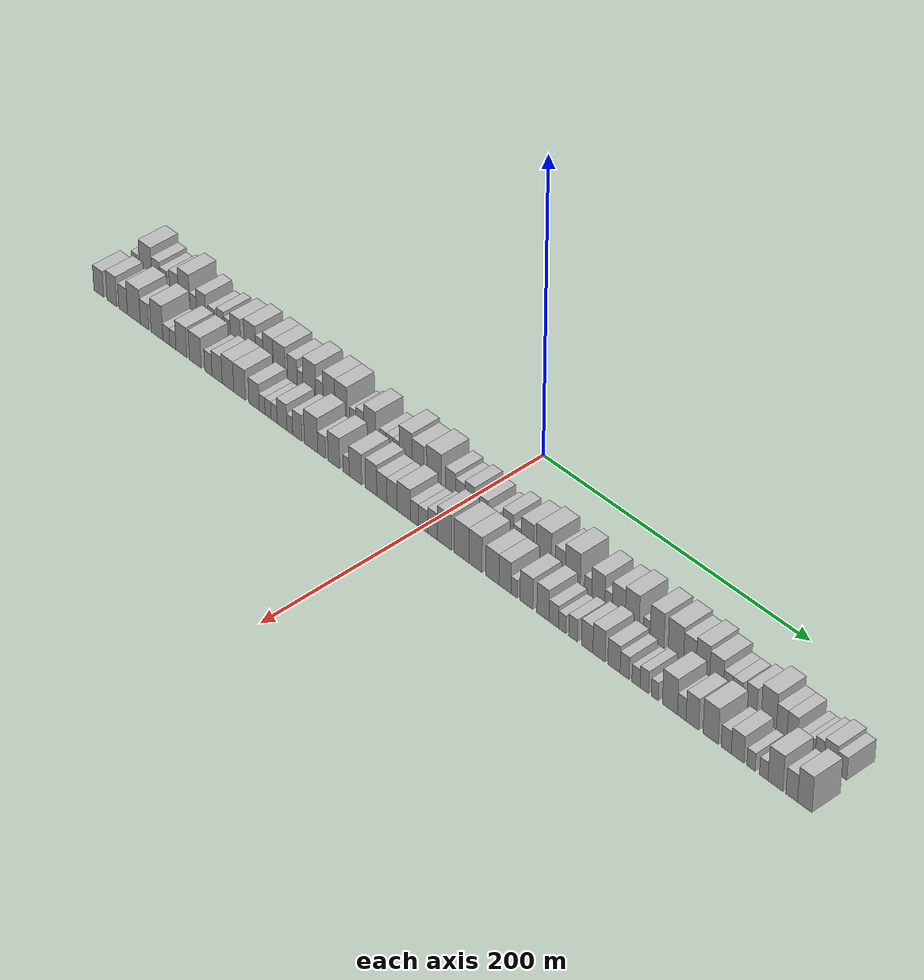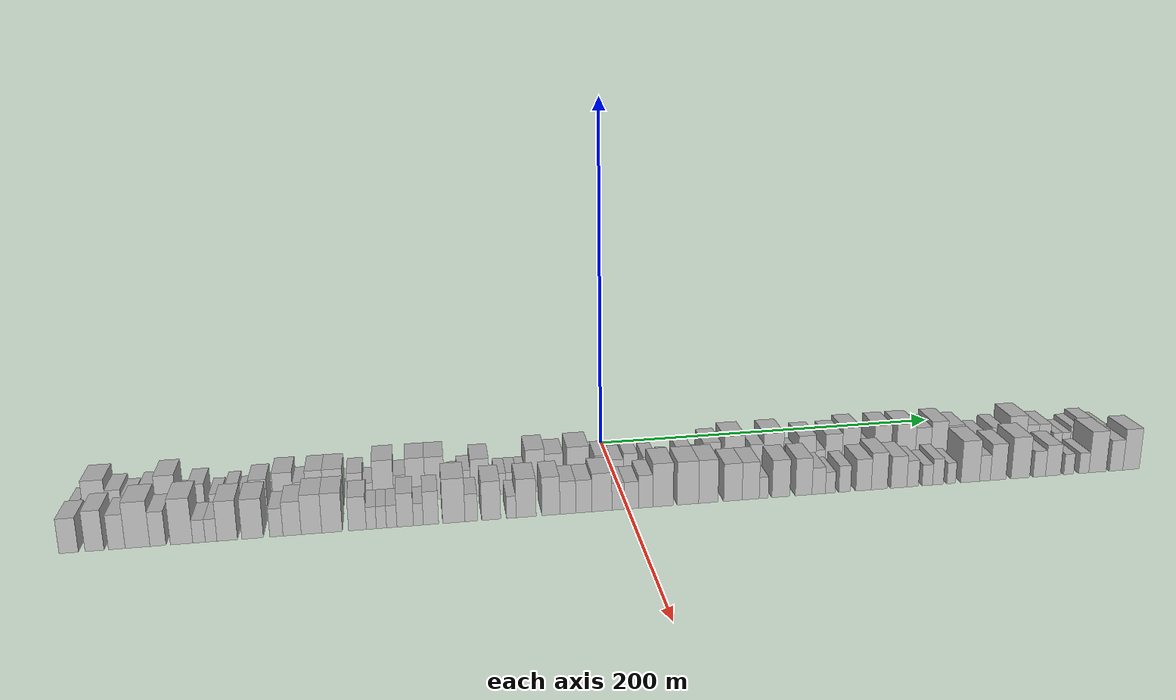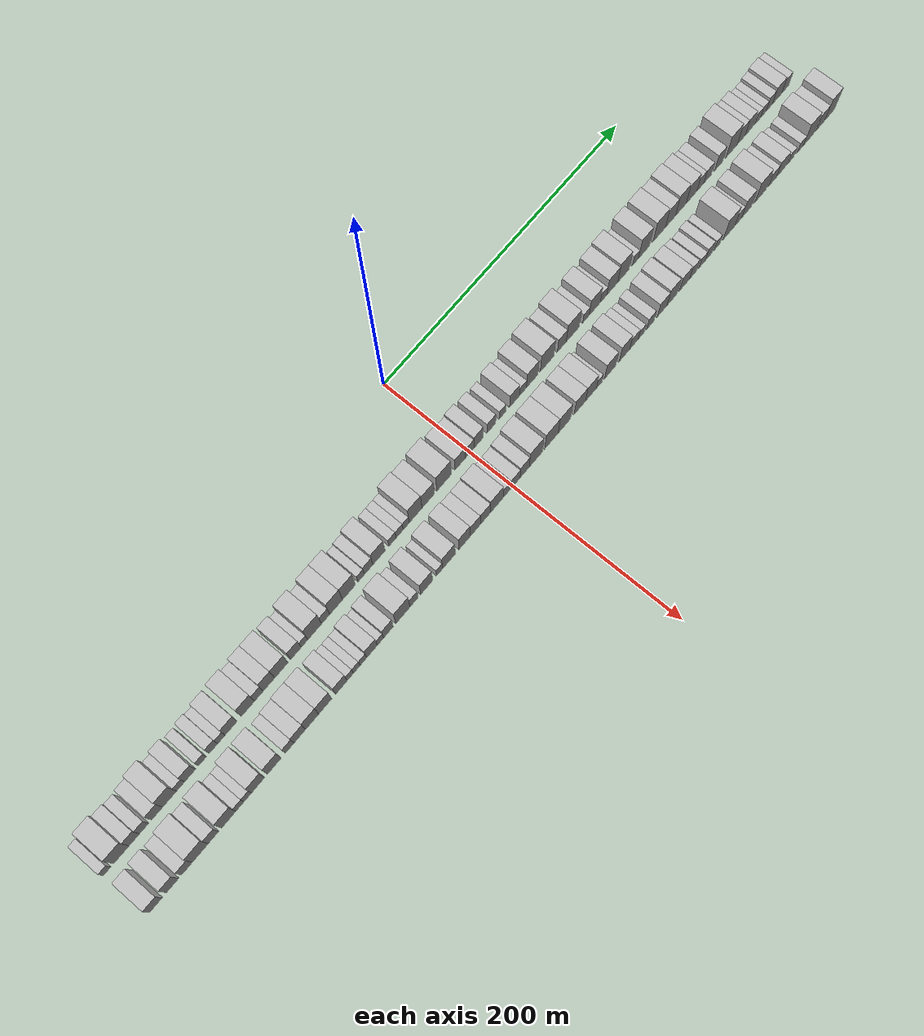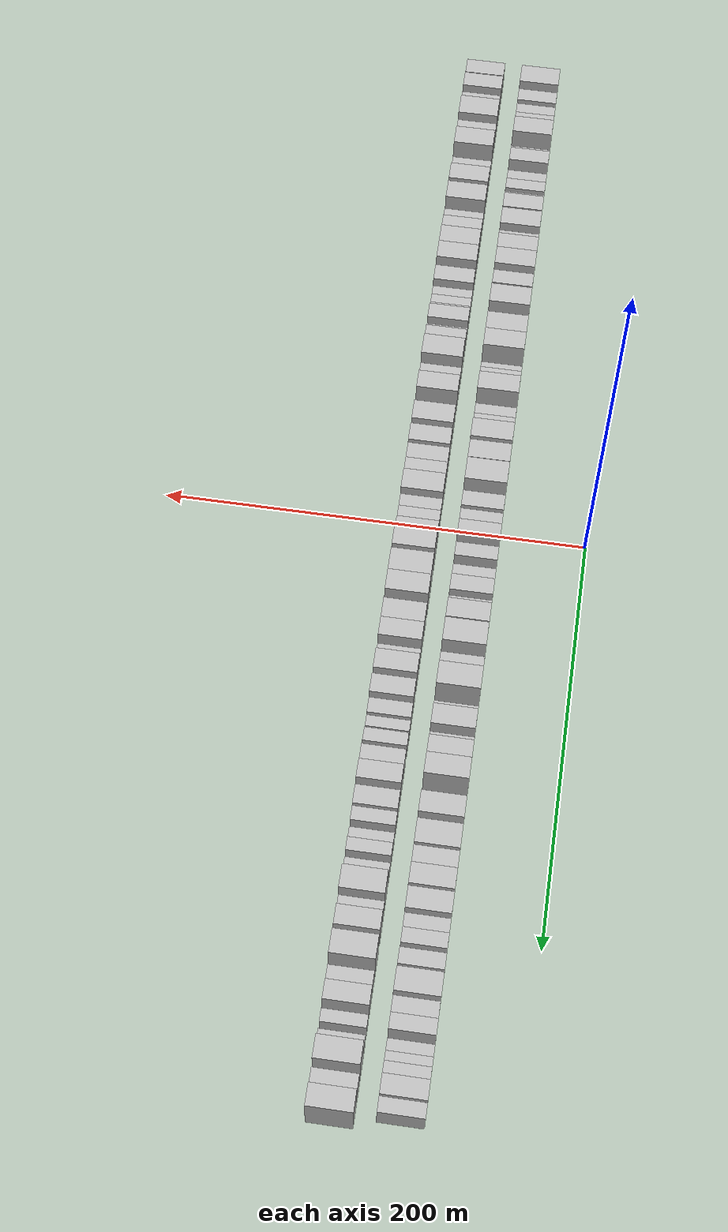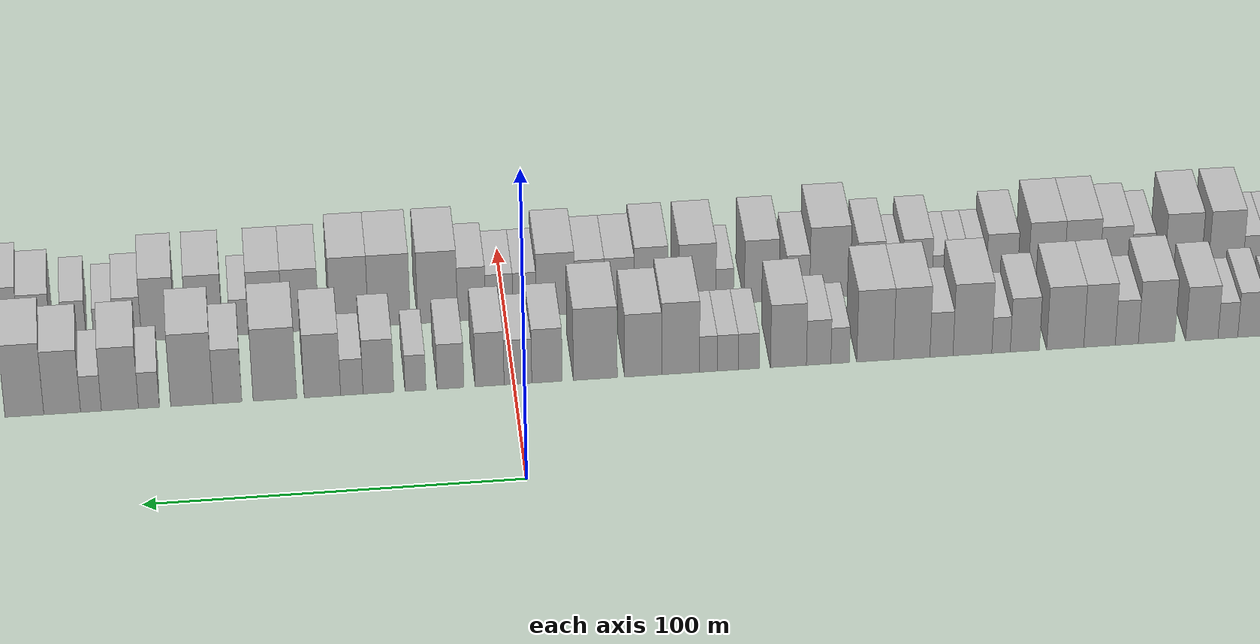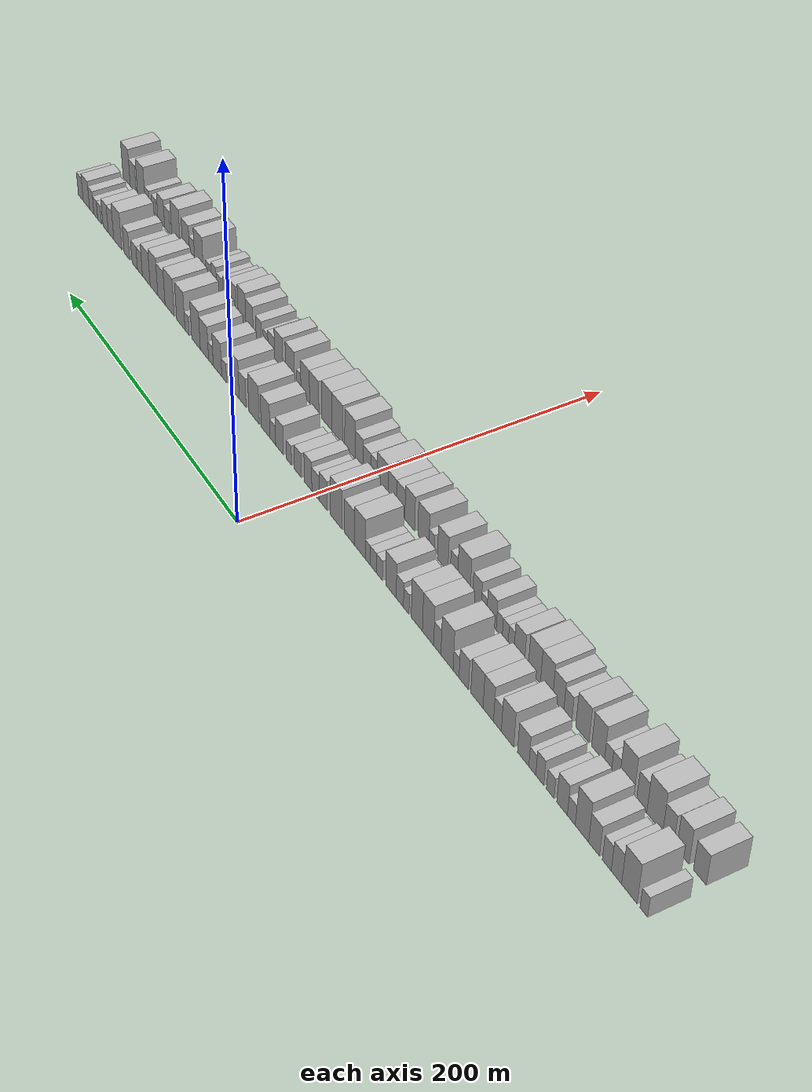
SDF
<sdf version="1.6">
 <world name="default">
  <scene>
   <sky><clouds><speed>12</speed></clouds></sky>
   <ambient>0.4 0.4 0.4 1</ambient>
   <background>0.7 0.7 0.7 1</background>
   <shadows>1</shadows>
  </scene>
  <gravity>0 0 -9.8066</gravity>
  <magnetic_field>6e-06 2.3e-05 -4.2e-05</magnetic_field>
  <physics default="0" name="default_physics" type="ode">
   <ode>
    <solver>
     <type>quick</type>
     <iters>10</iters>
     <sor>1.0</sor>
     <use_dynamic_moi_rescaling>0</use_dynamic_moi_rescaling>
    </solver>
    <constraints>
     <cfm>0</cfm>
     <erp>0.2</erp>
     <contact_max_correcting_vel>100</contact_max_correcting_vel>
     <contact_surface_layer>0.001</contact_surface_layer>
    </constraints>
   </ode>
   <max_step_size>0.004</max_step_size>
   <real_time_factor>1</real_time_factor>
   <real_time_update_rate>250</real_time_update_rate>
  </physics>
  <light name="sun" type="directional">
   <pose>0 0 10 0 0 0</pose>
   <diffuse>0.8 0.8 0.8 1</diffuse>
   <specular>0.2 0.2 0.2 1</specular>
   <attenuation>
    <range>1000</range>
    <constant>0.9</constant>
    <linear>0.01</linear>
    <quadratic>0.001</quadratic>
   </attenuation>
   <direction>-0.5 0.1 -0.9</direction>
  </light>
  <model name="building_1">
   <static>1</static>
   <pose>50.0000 -275.3579 0 0.000000 0.000000 0.000000</pose>
   <link name="link">
    <pose>0 0 6.00 0 0 0</pose>
    <collision name="collision"><geometry><box><size>20.0000 5.2843 12.0000</size></box></geometry></collision>
    <visual name="visual">
     <cast_shadows>0</cast_shadows>
     <geometry><box><size>20.0000 5.2843 12.0000</size></box></geometry>
     <material>
      <script>
       <uri>model://HANNAS_wall/materials/scripts</uri>
       <uri>model://HANNAS_wall/materials/textures</uri>
       <name>vrc/HANNAS_wall</name>
      </script>
     </material>
    </visual>
   </link>
  </model>
  <model name="building_2">
   <static>1</static>
   <pose>50.0000 -265.2781 0 0.000000 0.000000 0.000000</pose>
   <link name="link">
    <pose>0 0 12.00 0 0 0</pose>
    <collision name="collision"><geometry><box><size>20.0000 10.8752 24.0000</size></box></geometry></collision>
    <visual name="visual">
     <cast_shadows>0</cast_shadows>
     <geometry><box><size>20.0000 10.8752 24.0000</size></box></geometry>
     <material>
      <script>
       <uri>model://HANNAS_wall/materials/scripts</uri>
       <uri>model://HANNAS_wall/materials/textures</uri>
       <name>vrc/HANNAS_wall</name>
      </script>
     </material>
    </visual>
   </link>
  </model>
  <model name="building_3">
   <static>1</static>
   <pose>50.0000 -256.1429 0 0.000000 0.000000 0.000000</pose>
   <link name="link">
    <pose>0 0 9.00 0 0 0</pose>
    <collision name="collision"><geometry><box><size>20.0000 7.3953 18.0000</size></box></geometry></collision>
    <visual name="visual">
     <cast_shadows>0</cast_shadows>
     <geometry><box><size>20.0000 7.3953 18.0000</size></box></geometry>
     <material>
      <script>
       <uri>model://HANNAS_wall/materials/scripts</uri>
       <uri>model://HANNAS_wall/materials/textures</uri>
       <name>vrc/HANNAS_wall</name>
      </script>
     </material>
    </visual>
   </link>
  </model>
  <model name="building_4">
   <static>1</static>
   <pose>50.0000 -249.2715 0 0.000000 0.000000 0.000000</pose>
   <link name="link">
    <pose>0 0 7.50 0 0 0</pose>
    <collision name="collision"><geometry><box><size>20.0000 6.3475 15.0000</size></box></geometry></collision>
    <visual name="visual">
     <cast_shadows>0</cast_shadows>
     <geometry><box><size>20.0000 6.3475 15.0000</size></box></geometry>
     <material>
      <script>
       <uri>model://HANNAS_wall/materials/scripts</uri>
       <uri>model://HANNAS_wall/materials/textures</uri>
       <name>vrc/HANNAS_wall</name>
      </script>
     </material>
    </visual>
   </link>
  </model>
  <model name="building_5">
   <static>1</static>
   <pose>50.0000 -240.1305 0 0.000000 0.000000 0.000000</pose>
   <link name="link">
    <pose>0 0 9.00 0 0 0</pose>
    <collision name="collision"><geometry><box><size>20.0000 7.9344 18.0000</size></box></geometry></collision>
    <visual name="visual">
     <cast_shadows>0</cast_shadows>
     <geometry><box><size>20.0000 7.9344 18.0000</size></box></geometry>
     <material>
      <script>
       <uri>model://HANNAS_wall/materials/scripts</uri>
       <uri>model://HANNAS_wall/materials/textures</uri>
       <name>vrc/HANNAS_wall</name>
      </script>
     </material>
    </visual>
   </link>
  </model>
  <model name="building_6">
   <static>1</static>
   <pose>50.0000 -231.2084 0 0.000000 0.000000 0.000000</pose>
   <link name="link">
    <pose>0 0 12.00 0 0 0</pose>
    <collision name="collision"><geometry><box><size>20.0000 9.9098 24.0000</size></box></geometry></collision>
    <visual name="visual">
     <cast_shadows>0</cast_shadows>
     <geometry><box><size>20.0000 9.9098 24.0000</size></box></geometry>
     <material>
      <script>
       <uri>model://HANNAS_wall/materials/scripts</uri>
       <uri>model://HANNAS_wall/materials/textures</uri>
       <name>vrc/HANNAS_wall</name>
      </script>
     </material>
    </visual>
   </link>
  </model>
  <model name="building_7">
   <static>1</static>
   <pose>50.0000 -223.3316 0 0.000000 0.000000 0.000000</pose>
   <link name="link">
    <pose>0 0 6.00 0 0 0</pose>
    <collision name="collision"><geometry><box><size>20.0000 5.8438 12.0000</size></box></geometry></collision>
    <visual name="visual">
     <cast_shadows>0</cast_shadows>
     <geometry><box><size>20.0000 5.8438 12.0000</size></box></geometry>
     <material>
      <script>
       <uri>model://HANNAS_wall/materials/scripts</uri>
       <uri>model://HANNAS_wall/materials/textures</uri>
       <name>vrc/HANNAS_wall</name>
      </script>
     </material>
    </visual>
   </link>
  </model>
  <model name="building_8">
   <static>1</static>
   <pose>50.0000 -216.3932 0 0.000000 0.000000 0.000000</pose>
   <link name="link">
    <pose>0 0 9.00 0 0 0</pose>
    <collision name="collision"><geometry><box><size>20.0000 8.0331 18.0000</size></box></geometry></collision>
    <visual name="visual">
     <cast_shadows>0</cast_shadows>
     <geometry><box><size>20.0000 8.0331 18.0000</size></box></geometry>
     <material>
      <script>
       <uri>model://HANNAS_wall/materials/scripts</uri>
       <uri>model://HANNAS_wall/materials/textures</uri>
       <name>vrc/HANNAS_wall</name>
      </script>
     </material>
    </visual>
   </link>
  </model>
  <model name="building_9">
   <static>1</static>
   <pose>50.0000 -207.4719 0 0.000000 0.000000 0.000000</pose>
   <link name="link">
    <pose>0 0 6.00 0 0 0</pose>
    <collision name="collision"><geometry><box><size>20.0000 5.8093 12.0000</size></box></geometry></collision>
    <visual name="visual">
     <cast_shadows>0</cast_shadows>
     <geometry><box><size>20.0000 5.8093 12.0000</size></box></geometry>
     <material>
      <script>
       <uri>model://HANNAS_wall/materials/scripts</uri>
       <uri>model://HANNAS_wall/materials/textures</uri>
       <name>vrc/HANNAS_wall</name>
      </script>
     </material>
    </visual>
   </link>
  </model>
  <model name="building_10">
   <static>1</static>
   <pose>50.0000 -199.4390 0 0.000000 0.000000 0.000000</pose>
   <link name="link">
    <pose>0 0 7.50 0 0 0</pose>
    <collision name="collision"><geometry><box><size>20.0000 6.2564 15.0000</size></box></geometry></collision>
    <visual name="visual">
     <cast_shadows>0</cast_shadows>
     <geometry><box><size>20.0000 6.2564 15.0000</size></box></geometry>
     <material>
      <script>
       <uri>model://HANNAS_wall/materials/scripts</uri>
       <uri>model://HANNAS_wall/materials/textures</uri>
       <name>vrc/HANNAS_wall</name>
      </script>
     </material>
    </visual>
   </link>
  </model>
  <model name="building_11">
   <static>1</static>
   <pose>50.0000 -193.6024 0 0.000000 0.000000 0.000000</pose>
   <link name="link">
    <pose>0 0 6.00 0 0 0</pose>
    <collision name="collision"><geometry><box><size>20.0000 5.4169 12.0000</size></box></geometry></collision>
    <visual name="visual">
     <cast_shadows>0</cast_shadows>
     <geometry><box><size>20.0000 5.4169 12.0000</size></box></geometry>
     <material>
      <script>
       <uri>model://HANNAS_wall/materials/scripts</uri>
       <uri>model://HANNAS_wall/materials/textures</uri>
       <name>vrc/HANNAS_wall</name>
      </script>
     </material>
    </visual>
   </link>
  </model>
  <model name="building_12">
   <static>1</static>
   <pose>50.0000 -186.4434 0 0.000000 0.000000 0.000000</pose>
   <link name="link">
    <pose>0 0 9.00 0 0 0</pose>
    <collision name="collision"><geometry><box><size>20.0000 8.9011 18.0000</size></box></geometry></collision>
    <visual name="visual">
     <cast_shadows>0</cast_shadows>
     <geometry><box><size>20.0000 8.9011 18.0000</size></box></geometry>
     <material>
      <script>
       <uri>model://HANNAS_wall/materials/scripts</uri>
       <uri>model://HANNAS_wall/materials/textures</uri>
       <name>vrc/HANNAS_wall</name>
      </script>
     </material>
    </visual>
   </link>
  </model>
  <model name="building_13">
   <static>1</static>
   <pose>50.0000 -174.0192 0 0.000000 0.000000 0.000000</pose>
   <link name="link">
    <pose>0 0 10.50 0 0 0</pose>
    <collision name="collision"><geometry><box><size>20.0000 9.9473 21.0000</size></box></geometry></collision>
    <visual name="visual">
     <cast_shadows>0</cast_shadows>
     <geometry><box><size>20.0000 9.9473 21.0000</size></box></geometry>
     <material>
      <script>
       <uri>model://HANNAS_wall/materials/scripts</uri>
       <uri>model://HANNAS_wall/materials/textures</uri>
       <name>vrc/HANNAS_wall</name>
      </script>
     </material>
    </visual>
   </link>
  </model>
  <model name="building_14">
   <static>1</static>
   <pose>50.0000 -165.8925 0 0.000000 0.000000 0.000000</pose>
   <link name="link">
    <pose>0 0 7.50 0 0 0</pose>
    <collision name="collision"><geometry><box><size>20.0000 6.3062 15.0000</size></box></geometry></collision>
    <visual name="visual">
     <cast_shadows>0</cast_shadows>
     <geometry><box><size>20.0000 6.3062 15.0000</size></box></geometry>
     <material>
      <script>
       <uri>model://HANNAS_wall/materials/scripts</uri>
       <uri>model://HANNAS_wall/materials/textures</uri>
       <name>vrc/HANNAS_wall</name>
      </script>
     </material>
    </visual>
   </link>
  </model>
  <model name="building_15">
   <static>1</static>
   <pose>50.0000 -158.4266 0 0.000000 0.000000 0.000000</pose>
   <link name="link">
    <pose>0 0 10.50 0 0 0</pose>
    <collision name="collision"><geometry><box><size>20.0000 8.6257 21.0000</size></box></geometry></collision>
    <visual name="visual">
     <cast_shadows>0</cast_shadows>
     <geometry><box><size>20.0000 8.6257 21.0000</size></box></geometry>
     <material>
      <script>
       <uri>model://HANNAS_wall/materials/scripts</uri>
       <uri>model://HANNAS_wall/materials/textures</uri>
       <name>vrc/HANNAS_wall</name>
      </script>
     </material>
    </visual>
   </link>
  </model>
  <model name="building_16">
   <static>1</static>
   <pose>50.0000 -149.0510 0 0.000000 0.000000 0.000000</pose>
   <link name="link">
    <pose>0 0 10.50 0 0 0</pose>
    <collision name="collision"><geometry><box><size>20.0000 10.1255 21.0000</size></box></geometry></collision>
    <visual name="visual">
     <cast_shadows>0</cast_shadows>
     <geometry><box><size>20.0000 10.1255 21.0000</size></box></geometry>
     <material>
      <script>
       <uri>model://HANNAS_wall/materials/scripts</uri>
       <uri>model://HANNAS_wall/materials/textures</uri>
       <name>vrc/HANNAS_wall</name>
      </script>
     </material>
    </visual>
   </link>
  </model>
  <model name="building_17">
   <static>1</static>
   <pose>50.0000 -138.0163 0 0.000000 0.000000 0.000000</pose>
   <link name="link">
    <pose>0 0 9.00 0 0 0</pose>
    <collision name="collision"><geometry><box><size>20.0000 7.9438 18.0000</size></box></geometry></collision>
    <visual name="visual">
     <cast_shadows>0</cast_shadows>
     <geometry><box><size>20.0000 7.9438 18.0000</size></box></geometry>
     <material>
      <script>
       <uri>model://HANNAS_wall/materials/scripts</uri>
       <uri>model://HANNAS_wall/materials/textures</uri>
       <name>vrc/HANNAS_wall</name>
      </script>
     </material>
    </visual>
   </link>
  </model>
  <model name="building_18">
   <static>1</static>
   <pose>50.0000 -131.5316 0 0.000000 0.000000 0.000000</pose>
   <link name="link">
    <pose>0 0 6.00 0 0 0</pose>
    <collision name="collision"><geometry><box><size>20.0000 5.0256 12.0000</size></box></geometry></collision>
    <visual name="visual">
     <cast_shadows>0</cast_shadows>
     <geometry><box><size>20.0000 5.0256 12.0000</size></box></geometry>
     <material>
      <script>
       <uri>model://HANNAS_wall/materials/scripts</uri>
       <uri>model://HANNAS_wall/materials/textures</uri>
       <name>vrc/HANNAS_wall</name>
      </script>
     </material>
    </visual>
   </link>
  </model>
  <model name="building_19">
   <static>1</static>
   <pose>50.0000 -123.7338 0 0.000000 0.000000 0.000000</pose>
   <link name="link">
    <pose>0 0 12.00 0 0 0</pose>
    <collision name="collision"><geometry><box><size>20.0000 10.5699 24.0000</size></box></geometry></collision>
    <visual name="visual">
     <cast_shadows>0</cast_shadows>
     <geometry><box><size>20.0000 10.5699 24.0000</size></box></geometry>
     <material>
      <script>
       <uri>model://HANNAS_wall/materials/scripts</uri>
       <uri>model://HANNAS_wall/materials/textures</uri>
       <name>vrc/HANNAS_wall</name>
      </script>
     </material>
    </visual>
   </link>
  </model>
  <model name="building_20">
   <static>1</static>
   <pose>50.0000 -115.3084 0 0.000000 0.000000 0.000000</pose>
   <link name="link">
    <pose>0 0 7.50 0 0 0</pose>
    <collision name="collision"><geometry><box><size>20.0000 6.2810 15.0000</size></box></geometry></collision>
    <visual name="visual">
     <cast_shadows>0</cast_shadows>
     <geometry><box><size>20.0000 6.2810 15.0000</size></box></geometry>
     <material>
      <script>
       <uri>model://HANNAS_wall/materials/scripts</uri>
       <uri>model://HANNAS_wall/materials/textures</uri>
       <name>vrc/HANNAS_wall</name>
      </script>
     </material>
    </visual>
   </link>
  </model>
  <model name="building_21">
   <static>1</static>
   <pose>50.0000 -107.2324 0 0.000000 0.000000 0.000000</pose>
   <link name="link">
    <pose>0 0 12.00 0 0 0</pose>
    <collision name="collision"><geometry><box><size>20.0000 9.8711 24.0000</size></box></geometry></collision>
    <visual name="visual">
     <cast_shadows>0</cast_shadows>
     <geometry><box><size>20.0000 9.8711 24.0000</size></box></geometry>
     <material>
      <script>
       <uri>model://HANNAS_wall/materials/scripts</uri>
       <uri>model://HANNAS_wall/materials/textures</uri>
       <name>vrc/HANNAS_wall</name>
      </script>
     </material>
    </visual>
   </link>
  </model>
  <model name="building_22">
   <static>1</static>
   <pose>50.0000 -97.2972 0 0.000000 0.000000 0.000000</pose>
   <link name="link">
    <pose>0 0 12.00 0 0 0</pose>
    <collision name="collision"><geometry><box><size>20.0000 9.9993 24.0000</size></box></geometry></collision>
    <visual name="visual">
     <cast_shadows>0</cast_shadows>
     <geometry><box><size>20.0000 9.9993 24.0000</size></box></geometry>
     <material>
      <script>
       <uri>model://HANNAS_wall/materials/scripts</uri>
       <uri>model://HANNAS_wall/materials/textures</uri>
       <name>vrc/HANNAS_wall</name>
      </script>
     </material>
    </visual>
   </link>
  </model>
  <model name="building_23">
   <static>1</static>
   <pose>50.0000 -87.7939 0 0.000000 0.000000 0.000000</pose>
   <link name="link">
    <pose>0 0 6.00 0 0 0</pose>
    <collision name="collision"><geometry><box><size>20.0000 5.0073 12.0000</size></box></geometry></collision>
    <visual name="visual">
     <cast_shadows>0</cast_shadows>
     <geometry><box><size>20.0000 5.0073 12.0000</size></box></geometry>
     <material>
      <script>
       <uri>model://HANNAS_wall/materials/scripts</uri>
       <uri>model://HANNAS_wall/materials/textures</uri>
       <name>vrc/HANNAS_wall</name>
      </script>
     </material>
    </visual>
   </link>
  </model>
  <model name="building_24">
   <static>1</static>
   <pose>50.0000 -81.9762 0 0.000000 0.000000 0.000000</pose>
   <link name="link">
    <pose>0 0 7.50 0 0 0</pose>
    <collision name="collision"><geometry><box><size>20.0000 6.6281 15.0000</size></box></geometry></collision>
    <visual name="visual">
     <cast_shadows>0</cast_shadows>
     <geometry><box><size>20.0000 6.6281 15.0000</size></box></geometry>
     <material>
      <script>
       <uri>model://HANNAS_wall/materials/scripts</uri>
       <uri>model://HANNAS_wall/materials/textures</uri>
       <name>vrc/HANNAS_wall</name>
      </script>
     </material>
    </visual>
   </link>
  </model>
  <model name="building_25">
   <static>1</static>
   <pose>50.0000 -73.7933 0 0.000000 0.000000 0.000000</pose>
   <link name="link">
    <pose>0 0 10.50 0 0 0</pose>
    <collision name="collision"><geometry><box><size>20.0000 9.7376 21.0000</size></box></geometry></collision>
    <visual name="visual">
     <cast_shadows>0</cast_shadows>
     <geometry><box><size>20.0000 9.7376 21.0000</size></box></geometry>
     <material>
      <script>
       <uri>model://HANNAS_wall/materials/scripts</uri>
       <uri>model://HANNAS_wall/materials/textures</uri>
       <name>vrc/HANNAS_wall</name>
      </script>
     </material>
    </visual>
   </link>
  </model>
  <model name="building_26">
   <static>1</static>
   <pose>50.0000 -63.0612 0 0.000000 0.000000 0.000000</pose>
   <link name="link">
    <pose>0 0 6.00 0 0 0</pose>
    <collision name="collision"><geometry><box><size>20.0000 5.7266 12.0000</size></box></geometry></collision>
    <visual name="visual">
     <cast_shadows>0</cast_shadows>
     <geometry><box><size>20.0000 5.7266 12.0000</size></box></geometry>
     <material>
      <script>
       <uri>model://HANNAS_wall/materials/scripts</uri>
       <uri>model://HANNAS_wall/materials/textures</uri>
       <name>vrc/HANNAS_wall</name>
      </script>
     </material>
    </visual>
   </link>
  </model>
  <model name="building_27">
   <static>1</static>
   <pose>50.0000 -57.3837 0 0.000000 0.000000 0.000000</pose>
   <link name="link">
    <pose>0 0 6.00 0 0 0</pose>
    <collision name="collision"><geometry><box><size>20.0000 5.6284 12.0000</size></box></geometry></collision>
    <visual name="visual">
     <cast_shadows>0</cast_shadows>
     <geometry><box><size>20.0000 5.6284 12.0000</size></box></geometry>
     <material>
      <script>
       <uri>model://HANNAS_wall/materials/scripts</uri>
       <uri>model://HANNAS_wall/materials/textures</uri>
       <name>vrc/HANNAS_wall</name>
      </script>
     </material>
    </visual>
   </link>
  </model>
  <model name="building_28">
   <static>1</static>
   <pose>50.0000 -52.1638 0 0.000000 0.000000 0.000000</pose>
   <link name="link">
    <pose>0 0 6.00 0 0 0</pose>
    <collision name="collision"><geometry><box><size>20.0000 4.8116 12.0000</size></box></geometry></collision>
    <visual name="visual">
     <cast_shadows>0</cast_shadows>
     <geometry><box><size>20.0000 4.8116 12.0000</size></box></geometry>
     <material>
      <script>
       <uri>model://HANNAS_wall/materials/scripts</uri>
       <uri>model://HANNAS_wall/materials/textures</uri>
       <name>vrc/HANNAS_wall</name>
      </script>
     </material>
    </visual>
   </link>
  </model>
  <model name="building_29">
   <static>1</static>
   <pose>50.0000 -44.6425 0 0.000000 0.000000 0.000000</pose>
   <link name="link">
    <pose>0 0 12.00 0 0 0</pose>
    <collision name="collision"><geometry><box><size>20.0000 10.2310 24.0000</size></box></geometry></collision>
    <visual name="visual">
     <cast_shadows>0</cast_shadows>
     <geometry><box><size>20.0000 10.2310 24.0000</size></box></geometry>
     <material>
      <script>
       <uri>model://HANNAS_wall/materials/scripts</uri>
       <uri>model://HANNAS_wall/materials/textures</uri>
       <name>vrc/HANNAS_wall</name>
      </script>
     </material>
    </visual>
   </link>
  </model>
  <model name="building_30">
   <static>1</static>
   <pose>50.0000 -34.5678 0 0.000000 0.000000 0.000000</pose>
   <link name="link">
    <pose>0 0 10.50 0 0 0</pose>
    <collision name="collision"><geometry><box><size>20.0000 9.9183 21.0000</size></box></geometry></collision>
    <visual name="visual">
     <cast_shadows>0</cast_shadows>
     <geometry><box><size>20.0000 9.9183 21.0000</size></box></geometry>
     <material>
      <script>
       <uri>model://HANNAS_wall/materials/scripts</uri>
       <uri>model://HANNAS_wall/materials/textures</uri>
       <name>vrc/HANNAS_wall</name>
      </script>
     </material>
    </visual>
   </link>
  </model>
  <model name="building_31">
   <static>1</static>
   <pose>50.0000 -21.7144 0 0.000000 0.000000 0.000000</pose>
   <link name="link">
    <pose>0 0 12.00 0 0 0</pose>
    <collision name="collision"><geometry><box><size>20.0000 11.7885 24.0000</size></box></geometry></collision>
    <visual name="visual">
     <cast_shadows>0</cast_shadows>
     <geometry><box><size>20.0000 11.7885 24.0000</size></box></geometry>
     <material>
      <script>
       <uri>model://HANNAS_wall/materials/scripts</uri>
       <uri>model://HANNAS_wall/materials/textures</uri>
       <name>vrc/HANNAS_wall</name>
      </script>
     </material>
    </visual>
   </link>
  </model>
  <model name="building_32">
   <static>1</static>
   <pose>50.0000 -8.7360 0 0.000000 0.000000 0.000000</pose>
   <link name="link">
    <pose>0 0 9.00 0 0 0</pose>
    <collision name="collision"><geometry><box><size>20.0000 8.1682 18.0000</size></box></geometry></collision>
    <visual name="visual">
     <cast_shadows>0</cast_shadows>
     <geometry><box><size>20.0000 8.1682 18.0000</size></box></geometry>
     <material>
      <script>
       <uri>model://HANNAS_wall/materials/scripts</uri>
       <uri>model://HANNAS_wall/materials/textures</uri>
       <name>vrc/HANNAS_wall</name>
      </script>
     </material>
    </visual>
   </link>
  </model>
  <model name="building_33">
   <static>1</static>
   <pose>50.0000 -0.9373 0 0.000000 0.000000 0.000000</pose>
   <link name="link">
    <pose>0 0 7.50 0 0 0</pose>
    <collision name="collision"><geometry><box><size>20.0000 7.4293 15.0000</size></box></geometry></collision>
    <visual name="visual">
     <cast_shadows>0</cast_shadows>
     <geometry><box><size>20.0000 7.4293 15.0000</size></box></geometry>
     <material>
      <script>
       <uri>model://HANNAS_wall/materials/scripts</uri>
       <uri>model://HANNAS_wall/materials/textures</uri>
       <name>vrc/HANNAS_wall</name>
      </script>
     </material>
    </visual>
   </link>
  </model>
  <model name="building_34">
   <static>1</static>
   <pose>50.0000 6.6551 0 0.000000 0.000000 0.000000</pose>
   <link name="link">
    <pose>0 0 9.00 0 0 0</pose>
    <collision name="collision"><geometry><box><size>20.0000 7.7553 18.0000</size></box></geometry></collision>
    <visual name="visual">
     <cast_shadows>0</cast_shadows>
     <geometry><box><size>20.0000 7.7553 18.0000</size></box></geometry>
     <material>
      <script>
       <uri>model://HANNAS_wall/materials/scripts</uri>
       <uri>model://HANNAS_wall/materials/textures</uri>
       <name>vrc/HANNAS_wall</name>
      </script>
     </material>
    </visual>
   </link>
  </model>
  <model name="building_35">
   <static>1</static>
   <pose>50.0000 17.1252 0 0.000000 0.000000 0.000000</pose>
   <link name="link">
    <pose>0 0 7.50 0 0 0</pose>
    <collision name="collision"><geometry><box><size>20.0000 7.1849 15.0000</size></box></geometry></collision>
    <visual name="visual">
     <cast_shadows>0</cast_shadows>
     <geometry><box><size>20.0000 7.1849 15.0000</size></box></geometry>
     <material>
      <script>
       <uri>model://HANNAS_wall/materials/scripts</uri>
       <uri>model://HANNAS_wall/materials/textures</uri>
       <name>vrc/HANNAS_wall</name>
      </script>
     </material>
    </visual>
   </link>
  </model>
  <model name="building_36">
   <static>1</static>
   <pose>50.0000 26.4992 0 0.000000 0.000000 0.000000</pose>
   <link name="link">
    <pose>0 0 6.00 0 0 0</pose>
    <collision name="collision"><geometry><box><size>20.0000 5.5631 12.0000</size></box></geometry></collision>
    <visual name="visual">
     <cast_shadows>0</cast_shadows>
     <geometry><box><size>20.0000 5.5631 12.0000</size></box></geometry>
     <material>
      <script>
       <uri>model://HANNAS_wall/materials/scripts</uri>
       <uri>model://HANNAS_wall/materials/textures</uri>
       <name>vrc/HANNAS_wall</name>
      </script>
     </material>
    </visual>
   </link>
  </model>
  <model name="building_37">
   <static>1</static>
   <pose>50.0000 36.3989 0 0.000000 0.000000 0.000000</pose>
   <link name="link">
    <pose>0 0 9.00 0 0 0</pose>
    <collision name="collision"><geometry><box><size>20.0000 8.2364 18.0000</size></box></geometry></collision>
    <visual name="visual">
     <cast_shadows>0</cast_shadows>
     <geometry><box><size>20.0000 8.2364 18.0000</size></box></geometry>
     <material>
      <script>
       <uri>model://HANNAS_wall/materials/scripts</uri>
       <uri>model://HANNAS_wall/materials/textures</uri>
       <name>vrc/HANNAS_wall</name>
      </script>
     </material>
    </visual>
   </link>
  </model>
  <model name="building_38">
   <static>1</static>
   <pose>50.0000 43.5059 0 0.000000 0.000000 0.000000</pose>
   <link name="link">
    <pose>0 0 6.00 0 0 0</pose>
    <collision name="collision"><geometry><box><size>20.0000 5.9776 12.0000</size></box></geometry></collision>
    <visual name="visual">
     <cast_shadows>0</cast_shadows>
     <geometry><box><size>20.0000 5.9776 12.0000</size></box></geometry>
     <material>
      <script>
       <uri>model://HANNAS_wall/materials/scripts</uri>
       <uri>model://HANNAS_wall/materials/textures</uri>
       <name>vrc/HANNAS_wall</name>
      </script>
     </material>
    </visual>
   </link>
  </model>
  <model name="building_39">
   <static>1</static>
   <pose>50.0000 51.3330 0 0.000000 0.000000 0.000000</pose>
   <link name="link">
    <pose>0 0 10.50 0 0 0</pose>
    <collision name="collision"><geometry><box><size>20.0000 9.6765 21.0000</size></box></geometry></collision>
    <visual name="visual">
     <cast_shadows>0</cast_shadows>
     <geometry><box><size>20.0000 9.6765 21.0000</size></box></geometry>
     <material>
      <script>
       <uri>model://HANNAS_wall/materials/scripts</uri>
       <uri>model://HANNAS_wall/materials/textures</uri>
       <name>vrc/HANNAS_wall</name>
      </script>
     </material>
    </visual>
   </link>
  </model>
  <model name="building_40">
   <static>1</static>
   <pose>50.0000 63.9703 0 0.000000 0.000000 0.000000</pose>
   <link name="link">
    <pose>0 0 12.00 0 0 0</pose>
    <collision name="collision"><geometry><box><size>20.0000 11.5981 24.0000</size></box></geometry></collision>
    <visual name="visual">
     <cast_shadows>0</cast_shadows>
     <geometry><box><size>20.0000 11.5981 24.0000</size></box></geometry>
     <material>
      <script>
       <uri>model://HANNAS_wall/materials/scripts</uri>
       <uri>model://HANNAS_wall/materials/textures</uri>
       <name>vrc/HANNAS_wall</name>
      </script>
     </material>
    </visual>
   </link>
  </model>
  <model name="building_41">
   <static>1</static>
   <pose>50.0000 76.5834 0 0.000000 0.000000 0.000000</pose>
   <link name="link">
    <pose>0 0 9.00 0 0 0</pose>
    <collision name="collision"><geometry><box><size>20.0000 7.6281 18.0000</size></box></geometry></collision>
    <visual name="visual">
     <cast_shadows>0</cast_shadows>
     <geometry><box><size>20.0000 7.6281 18.0000</size></box></geometry>
     <material>
      <script>
       <uri>model://HANNAS_wall/materials/scripts</uri>
       <uri>model://HANNAS_wall/materials/textures</uri>
       <name>vrc/HANNAS_wall</name>
      </script>
     </material>
    </visual>
   </link>
  </model>
  <model name="building_42">
   <static>1</static>
   <pose>50.0000 86.0288 0 0.000000 0.000000 0.000000</pose>
   <link name="link">
    <pose>0 0 12.00 0 0 0</pose>
    <collision name="collision"><geometry><box><size>20.0000 11.2628 24.0000</size></box></geometry></collision>
    <visual name="visual">
     <cast_shadows>0</cast_shadows>
     <geometry><box><size>20.0000 11.2628 24.0000</size></box></geometry>
     <material>
      <script>
       <uri>model://HANNAS_wall/materials/scripts</uri>
       <uri>model://HANNAS_wall/materials/textures</uri>
       <name>vrc/HANNAS_wall</name>
      </script>
     </material>
    </visual>
   </link>
  </model>
  <model name="building_43">
   <static>1</static>
   <pose>50.0000 97.4271 0 0.000000 0.000000 0.000000</pose>
   <link name="link">
    <pose>0 0 6.00 0 0 0</pose>
    <collision name="collision"><geometry><box><size>20.0000 5.5338 12.0000</size></box></geometry></collision>
    <visual name="visual">
     <cast_shadows>0</cast_shadows>
     <geometry><box><size>20.0000 5.5338 12.0000</size></box></geometry>
     <material>
      <script>
       <uri>model://HANNAS_wall/materials/scripts</uri>
       <uri>model://HANNAS_wall/materials/textures</uri>
       <name>vrc/HANNAS_wall</name>
      </script>
     </material>
    </visual>
   </link>
  </model>
  <model name="building_44">
   <static>1</static>
   <pose>50.0000 105.1059 0 0.000000 0.000000 0.000000</pose>
   <link name="link">
    <pose>0 0 10.50 0 0 0</pose>
    <collision name="collision"><geometry><box><size>20.0000 9.8237 21.0000</size></box></geometry></collision>
    <visual name="visual">
     <cast_shadows>0</cast_shadows>
     <geometry><box><size>20.0000 9.8237 21.0000</size></box></geometry>
     <material>
      <script>
       <uri>model://HANNAS_wall/materials/scripts</uri>
       <uri>model://HANNAS_wall/materials/textures</uri>
       <name>vrc/HANNAS_wall</name>
      </script>
     </material>
    </visual>
   </link>
  </model>
  <model name="building_45">
   <static>1</static>
   <pose>50.0000 112.7721 0 0.000000 0.000000 0.000000</pose>
   <link name="link">
    <pose>0 0 6.00 0 0 0</pose>
    <collision name="collision"><geometry><box><size>20.0000 5.5086 12.0000</size></box></geometry></collision>
    <visual name="visual">
     <cast_shadows>0</cast_shadows>
     <geometry><box><size>20.0000 5.5086 12.0000</size></box></geometry>
     <material>
      <script>
       <uri>model://HANNAS_wall/materials/scripts</uri>
       <uri>model://HANNAS_wall/materials/textures</uri>
       <name>vrc/HANNAS_wall</name>
      </script>
     </material>
    </visual>
   </link>
  </model>
  <model name="building_46">
   <static>1</static>
   <pose>50.0000 120.3846 0 0.000000 0.000000 0.000000</pose>
   <link name="link">
    <pose>0 0 10.50 0 0 0</pose>
    <collision name="collision"><geometry><box><size>20.0000 9.7165 21.0000</size></box></geometry></collision>
    <visual name="visual">
     <cast_shadows>0</cast_shadows>
     <geometry><box><size>20.0000 9.7165 21.0000</size></box></geometry>
     <material>
      <script>
       <uri>model://HANNAS_wall/materials/scripts</uri>
       <uri>model://HANNAS_wall/materials/textures</uri>
       <name>vrc/HANNAS_wall</name>
      </script>
     </material>
    </visual>
   </link>
  </model>
  <model name="building_47">
   <static>1</static>
   <pose>50.0000 130.3578 0 0.000000 0.000000 0.000000</pose>
   <link name="link">
    <pose>0 0 12.00 0 0 0</pose>
    <collision name="collision"><geometry><box><size>20.0000 10.2298 24.0000</size></box></geometry></collision>
    <visual name="visual">
     <cast_shadows>0</cast_shadows>
     <geometry><box><size>20.0000 10.2298 24.0000</size></box></geometry>
     <material>
      <script>
       <uri>model://HANNAS_wall/materials/scripts</uri>
       <uri>model://HANNAS_wall/materials/textures</uri>
       <name>vrc/HANNAS_wall</name>
      </script>
     </material>
    </visual>
   </link>
  </model>
  <model name="building_48">
   <static>1</static>
   <pose>50.0000 141.0433 0 0.000000 0.000000 0.000000</pose>
   <link name="link">
    <pose>0 0 6.00 0 0 0</pose>
    <collision name="collision"><geometry><box><size>20.0000 5.1412 12.0000</size></box></geometry></collision>
    <visual name="visual">
     <cast_shadows>0</cast_shadows>
     <geometry><box><size>20.0000 5.1412 12.0000</size></box></geometry>
     <material>
      <script>
       <uri>model://HANNAS_wall/materials/scripts</uri>
       <uri>model://HANNAS_wall/materials/textures</uri>
       <name>vrc/HANNAS_wall</name>
      </script>
     </material>
    </visual>
   </link>
  </model>
  <model name="building_49">
   <static>1</static>
   <pose>50.0000 148.6736 0 0.000000 0.000000 0.000000</pose>
   <link name="link">
    <pose>0 0 12.00 0 0 0</pose>
    <collision name="collision"><geometry><box><size>20.0000 10.1195 24.0000</size></box></geometry></collision>
    <visual name="visual">
     <cast_shadows>0</cast_shadows>
     <geometry><box><size>20.0000 10.1195 24.0000</size></box></geometry>
     <material>
      <script>
       <uri>model://HANNAS_wall/materials/scripts</uri>
       <uri>model://HANNAS_wall/materials/textures</uri>
       <name>vrc/HANNAS_wall</name>
      </script>
     </material>
    </visual>
   </link>
  </model>
  <model name="building_50">
   <static>1</static>
   <pose>50.0000 162.3706 0 0.000000 0.000000 0.000000</pose>
   <link name="link">
    <pose>0 0 12.00 0 0 0</pose>
    <collision name="collision"><geometry><box><size>20.0000 11.2746 24.0000</size></box></geometry></collision>
    <visual name="visual">
     <cast_shadows>0</cast_shadows>
     <geometry><box><size>20.0000 11.2746 24.0000</size></box></geometry>
     <material>
      <script>
       <uri>model://HANNAS_wall/materials/scripts</uri>
       <uri>model://HANNAS_wall/materials/textures</uri>
       <name>vrc/HANNAS_wall</name>
      </script>
     </material>
    </visual>
   </link>
  </model>
  <model name="building_51">
   <static>1</static>
   <pose>50.0000 172.5475 0 0.000000 0.000000 0.000000</pose>
   <link name="link">
    <pose>0 0 10.50 0 0 0</pose>
    <collision name="collision"><geometry><box><size>20.0000 9.0792 21.0000</size></box></geometry></collision>
    <visual name="visual">
     <cast_shadows>0</cast_shadows>
     <geometry><box><size>20.0000 9.0792 21.0000</size></box></geometry>
     <material>
      <script>
       <uri>model://HANNAS_wall/materials/scripts</uri>
       <uri>model://HANNAS_wall/materials/textures</uri>
       <name>vrc/HANNAS_wall</name>
      </script>
     </material>
    </visual>
   </link>
  </model>
  <model name="building_52">
   <static>1</static>
   <pose>50.0000 181.9279 0 0.000000 0.000000 0.000000</pose>
   <link name="link">
    <pose>0 0 12.00 0 0 0</pose>
    <collision name="collision"><geometry><box><size>20.0000 9.6816 24.0000</size></box></geometry></collision>
    <visual name="visual">
     <cast_shadows>0</cast_shadows>
     <geometry><box><size>20.0000 9.6816 24.0000</size></box></geometry>
     <material>
      <script>
       <uri>model://HANNAS_wall/materials/scripts</uri>
       <uri>model://HANNAS_wall/materials/textures</uri>
       <name>vrc/HANNAS_wall</name>
      </script>
     </material>
    </visual>
   </link>
  </model>
  <model name="building_53">
   <static>1</static>
   <pose>50.0000 191.7421 0 0.000000 0.000000 0.000000</pose>
   <link name="link">
    <pose>0 0 10.50 0 0 0</pose>
    <collision name="collision"><geometry><box><size>20.0000 9.9468 21.0000</size></box></geometry></collision>
    <visual name="visual">
     <cast_shadows>0</cast_shadows>
     <geometry><box><size>20.0000 9.9468 21.0000</size></box></geometry>
     <material>
      <script>
       <uri>model://HANNAS_wall/materials/scripts</uri>
       <uri>model://HANNAS_wall/materials/textures</uri>
       <name>vrc/HANNAS_wall</name>
      </script>
     </material>
    </visual>
   </link>
  </model>
  <model name="building_54">
   <static>1</static>
   <pose>50.0000 199.9086 0 0.000000 0.000000 0.000000</pose>
   <link name="link">
    <pose>0 0 7.50 0 0 0</pose>
    <collision name="collision"><geometry><box><size>20.0000 6.3862 15.0000</size></box></geometry></collision>
    <visual name="visual">
     <cast_shadows>0</cast_shadows>
     <geometry><box><size>20.0000 6.3862 15.0000</size></box></geometry>
     <material>
      <script>
       <uri>model://HANNAS_wall/materials/scripts</uri>
       <uri>model://HANNAS_wall/materials/textures</uri>
       <name>vrc/HANNAS_wall</name>
      </script>
     </material>
    </visual>
   </link>
  </model>
  <model name="building_55">
   <static>1</static>
   <pose>50.0000 206.6260 0 0.000000 0.000000 0.000000</pose>
   <link name="link">
    <pose>0 0 7.50 0 0 0</pose>
    <collision name="collision"><geometry><box><size>20.0000 7.0486 15.0000</size></box></geometry></collision>
    <visual name="visual">
     <cast_shadows>0</cast_shadows>
     <geometry><box><size>20.0000 7.0486 15.0000</size></box></geometry>
     <material>
      <script>
       <uri>model://HANNAS_wall/materials/scripts</uri>
       <uri>model://HANNAS_wall/materials/textures</uri>
       <name>vrc/HANNAS_wall</name>
      </script>
     </material>
    </visual>
   </link>
  </model>
  <model name="building_56">
   <static>1</static>
   <pose>50.0000 216.8611 0 0.000000 0.000000 0.000000</pose>
   <link name="link">
    <pose>0 0 9.00 0 0 0</pose>
    <collision name="collision"><geometry><box><size>20.0000 7.4216 18.0000</size></box></geometry></collision>
    <visual name="visual">
     <cast_shadows>0</cast_shadows>
     <geometry><box><size>20.0000 7.4216 18.0000</size></box></geometry>
     <material>
      <script>
       <uri>model://HANNAS_wall/materials/scripts</uri>
       <uri>model://HANNAS_wall/materials/textures</uri>
       <name>vrc/HANNAS_wall</name>
      </script>
     </material>
    </visual>
   </link>
  </model>
  <model name="building_57">
   <static>1</static>
   <pose>50.0000 228.9514 0 0.000000 0.000000 0.000000</pose>
   <link name="link">
    <pose>0 0 12.00 0 0 0</pose>
    <collision name="collision"><geometry><box><size>20.0000 10.7588 24.0000</size></box></geometry></collision>
    <visual name="visual">
     <cast_shadows>0</cast_shadows>
     <geometry><box><size>20.0000 10.7588 24.0000</size></box></geometry>
     <material>
      <script>
       <uri>model://HANNAS_wall/materials/scripts</uri>
       <uri>model://HANNAS_wall/materials/textures</uri>
       <name>vrc/HANNAS_wall</name>
      </script>
     </material>
    </visual>
   </link>
  </model>
  <model name="building_58">
   <static>1</static>
   <pose>50.0000 237.9927 0 0.000000 0.000000 0.000000</pose>
   <link name="link">
    <pose>0 0 9.00 0 0 0</pose>
    <collision name="collision"><geometry><box><size>20.0000 7.3238 18.0000</size></box></geometry></collision>
    <visual name="visual">
     <cast_shadows>0</cast_shadows>
     <geometry><box><size>20.0000 7.3238 18.0000</size></box></geometry>
     <material>
      <script>
       <uri>model://HANNAS_wall/materials/scripts</uri>
       <uri>model://HANNAS_wall/materials/textures</uri>
       <name>vrc/HANNAS_wall</name>
      </script>
     </material>
    </visual>
   </link>
  </model>
  <model name="building_59">
   <static>1</static>
   <pose>50.0000 245.2843 0 0.000000 0.000000 0.000000</pose>
   <link name="link">
    <pose>0 0 9.00 0 0 0</pose>
    <collision name="collision"><geometry><box><size>20.0000 7.2594 18.0000</size></box></geometry></collision>
    <visual name="visual">
     <cast_shadows>0</cast_shadows>
     <geometry><box><size>20.0000 7.2594 18.0000</size></box></geometry>
     <material>
      <script>
       <uri>model://HANNAS_wall/materials/scripts</uri>
       <uri>model://HANNAS_wall/materials/textures</uri>
       <name>vrc/HANNAS_wall</name>
      </script>
     </material>
    </visual>
   </link>
  </model>
  <model name="building_60">
   <static>1</static>
   <pose>50.0000 253.5499 0 0.000000 0.000000 0.000000</pose>
   <link name="link">
    <pose>0 0 6.00 0 0 0</pose>
    <collision name="collision"><geometry><box><size>20.0000 5.2718 12.0000</size></box></geometry></collision>
    <visual name="visual">
     <cast_shadows>0</cast_shadows>
     <geometry><box><size>20.0000 5.2718 12.0000</size></box></geometry>
     <material>
      <script>
       <uri>model://HANNAS_wall/materials/scripts</uri>
       <uri>model://HANNAS_wall/materials/textures</uri>
       <name>vrc/HANNAS_wall</name>
      </script>
     </material>
    </visual>
   </link>
  </model>
  <model name="building_61">
   <static>1</static>
   <pose>50.0000 258.7676 0 0.000000 0.000000 0.000000</pose>
   <link name="link">
    <pose>0 0 6.00 0 0 0</pose>
    <collision name="collision"><geometry><box><size>20.0000 5.1638 12.0000</size></box></geometry></collision>
    <visual name="visual">
     <cast_shadows>0</cast_shadows>
     <geometry><box><size>20.0000 5.1638 12.0000</size></box></geometry>
     <material>
      <script>
       <uri>model://HANNAS_wall/materials/scripts</uri>
       <uri>model://HANNAS_wall/materials/textures</uri>
       <name>vrc/HANNAS_wall</name>
      </script>
     </material>
    </visual>
   </link>
  </model>
  <model name="building_62">
   <static>1</static>
   <pose>50.0000 264.3996 0 0.000000 0.000000 0.000000</pose>
   <link name="link">
    <pose>0 0 7.50 0 0 0</pose>
    <collision name="collision"><geometry><box><size>20.0000 6.1002 15.0000</size></box></geometry></collision>
    <visual name="visual">
     <cast_shadows>0</cast_shadows>
     <geometry><box><size>20.0000 6.1002 15.0000</size></box></geometry>
     <material>
      <script>
       <uri>model://HANNAS_wall/materials/scripts</uri>
       <uri>model://HANNAS_wall/materials/textures</uri>
       <name>vrc/HANNAS_wall</name>
      </script>
     </material>
    </visual>
   </link>
  </model>
  <model name="building_63">
   <static>1</static>
   <pose>50.0000 271.8828 0 0.000000 0.000000 0.000000</pose>
   <link name="link">
    <pose>0 0 9.00 0 0 0</pose>
    <collision name="collision"><geometry><box><size>20.0000 8.8662 18.0000</size></box></geometry></collision>
    <visual name="visual">
     <cast_shadows>0</cast_shadows>
     <geometry><box><size>20.0000 8.8662 18.0000</size></box></geometry>
     <material>
      <script>
       <uri>model://HANNAS_wall/materials/scripts</uri>
       <uri>model://HANNAS_wall/materials/textures</uri>
       <name>vrc/HANNAS_wall</name>
      </script>
     </material>
    </visual>
   </link>
  </model>
  <model name="building_64">
   <static>1</static>
   <pose>50.0000 279.7023 0 0.000000 0.000000 0.000000</pose>
   <link name="link">
    <pose>0 0 7.50 0 0 0</pose>
    <collision name="collision"><geometry><box><size>20.0000 6.7728 15.0000</size></box></geometry></collision>
    <visual name="visual">
     <cast_shadows>0</cast_shadows>
     <geometry><box><size>20.0000 6.7728 15.0000</size></box></geometry>
     <material>
      <script>
       <uri>model://HANNAS_wall/materials/scripts</uri>
       <uri>model://HANNAS_wall/materials/textures</uri>
       <name>vrc/HANNAS_wall</name>
      </script>
     </material>
    </visual>
   </link>
  </model>
  <model name="building_65">
   <static>1</static>
   <pose>79.0000 -271.6233 0 0.000000 0.000000 0.000000</pose>
   <link name="link">
    <pose>0 0 9.00 0 0 0</pose>
    <collision name="collision"><geometry><box><size>20.0000 8.7535 18.0000</size></box></geometry></collision>
    <visual name="visual">
     <cast_shadows>0</cast_shadows>
     <geometry><box><size>20.0000 8.7535 18.0000</size></box></geometry>
     <material>
      <script>
       <uri>model://HANNAS_wall/materials/scripts</uri>
       <uri>model://HANNAS_wall/materials/textures</uri>
       <name>vrc/HANNAS_wall</name>
      </script>
     </material>
    </visual>
   </link>
  </model>
  <model name="building_66">
   <static>1</static>
   <pose>79.0000 -259.9285 0 0.000000 0.000000 0.000000</pose>
   <link name="link">
    <pose>0 0 10.50 0 0 0</pose>
    <collision name="collision"><geometry><box><size>20.0000 8.6360 21.0000</size></box></geometry></collision>
    <visual name="visual">
     <cast_shadows>0</cast_shadows>
     <geometry><box><size>20.0000 8.6360 21.0000</size></box></geometry>
     <material>
      <script>
       <uri>model://HANNAS_wall/materials/scripts</uri>
       <uri>model://HANNAS_wall/materials/textures</uri>
       <name>vrc/HANNAS_wall</name>
      </script>
     </material>
    </visual>
   </link>
  </model>
  <model name="building_67">
   <static>1</static>
   <pose>79.0000 -249.7857 0 0.000000 0.000000 0.000000</pose>
   <link name="link">
    <pose>0 0 9.00 0 0 0</pose>
    <collision name="collision"><geometry><box><size>20.0000 7.6496 18.0000</size></box></geometry></collision>
    <visual name="visual">
     <cast_shadows>0</cast_shadows>
     <geometry><box><size>20.0000 7.6496 18.0000</size></box></geometry>
     <material>
      <script>
       <uri>model://HANNAS_wall/materials/scripts</uri>
       <uri>model://HANNAS_wall/materials/textures</uri>
       <name>vrc/HANNAS_wall</name>
      </script>
     </material>
    </visual>
   </link>
  </model>
  <model name="building_68">
   <static>1</static>
   <pose>79.0000 -240.2579 0 0.000000 0.000000 0.000000</pose>
   <link name="link">
    <pose>0 0 12.00 0 0 0</pose>
    <collision name="collision"><geometry><box><size>20.0000 11.4059 24.0000</size></box></geometry></collision>
    <visual name="visual">
     <cast_shadows>0</cast_shadows>
     <geometry><box><size>20.0000 11.4059 24.0000</size></box></geometry>
     <material>
      <script>
       <uri>model://HANNAS_wall/materials/scripts</uri>
       <uri>model://HANNAS_wall/materials/textures</uri>
       <name>vrc/HANNAS_wall</name>
      </script>
     </material>
    </visual>
   </link>
  </model>
  <model name="building_69">
   <static>1</static>
   <pose>79.0000 -230.8504 0 0.000000 0.000000 0.000000</pose>
   <link name="link">
    <pose>0 0 9.00 0 0 0</pose>
    <collision name="collision"><geometry><box><size>20.0000 7.4092 18.0000</size></box></geometry></collision>
    <visual name="visual">
     <cast_shadows>0</cast_shadows>
     <geometry><box><size>20.0000 7.4092 18.0000</size></box></geometry>
     <material>
      <script>
       <uri>model://HANNAS_wall/materials/scripts</uri>
       <uri>model://HANNAS_wall/materials/textures</uri>
       <name>vrc/HANNAS_wall</name>
      </script>
     </material>
    </visual>
   </link>
  </model>
  <model name="building_70">
   <static>1</static>
   <pose>79.0000 -219.9303 0 0.000000 0.000000 0.000000</pose>
   <link name="link">
    <pose>0 0 12.00 0 0 0</pose>
    <collision name="collision"><geometry><box><size>20.0000 10.4309 24.0000</size></box></geometry></collision>
    <visual name="visual">
     <cast_shadows>0</cast_shadows>
     <geometry><box><size>20.0000 10.4309 24.0000</size></box></geometry>
     <material>
      <script>
       <uri>model://HANNAS_wall/materials/scripts</uri>
       <uri>model://HANNAS_wall/materials/textures</uri>
       <name>vrc/HANNAS_wall</name>
      </script>
     </material>
    </visual>
   </link>
  </model>
  <model name="building_71">
   <static>1</static>
   <pose>79.0000 -211.7836 0 0.000000 0.000000 0.000000</pose>
   <link name="link">
    <pose>0 0 6.00 0 0 0</pose>
    <collision name="collision"><geometry><box><size>20.0000 5.8625 12.0000</size></box></geometry></collision>
    <visual name="visual">
     <cast_shadows>0</cast_shadows>
     <geometry><box><size>20.0000 5.8625 12.0000</size></box></geometry>
     <material>
      <script>
       <uri>model://HANNAS_wall/materials/scripts</uri>
       <uri>model://HANNAS_wall/materials/textures</uri>
       <name>vrc/HANNAS_wall</name>
      </script>
     </material>
    </visual>
   </link>
  </model>
  <model name="building_72">
   <static>1</static>
   <pose>79.0000 -206.1311 0 0.000000 0.000000 0.000000</pose>
   <link name="link">
    <pose>0 0 6.00 0 0 0</pose>
    <collision name="collision"><geometry><box><size>20.0000 5.4426 12.0000</size></box></geometry></collision>
    <visual name="visual">
     <cast_shadows>0</cast_shadows>
     <geometry><box><size>20.0000 5.4426 12.0000</size></box></geometry>
     <material>
      <script>
       <uri>model://HANNAS_wall/materials/scripts</uri>
       <uri>model://HANNAS_wall/materials/textures</uri>
       <name>vrc/HANNAS_wall</name>
      </script>
     </material>
    </visual>
   </link>
  </model>
  <model name="building_73">
   <static>1</static>
   <pose>79.0000 -198.5769 0 0.000000 0.000000 0.000000</pose>
   <link name="link">
    <pose>0 0 10.50 0 0 0</pose>
    <collision name="collision"><geometry><box><size>20.0000 9.6657 21.0000</size></box></geometry></collision>
    <visual name="visual">
     <cast_shadows>0</cast_shadows>
     <geometry><box><size>20.0000 9.6657 21.0000</size></box></geometry>
     <material>
      <script>
       <uri>model://HANNAS_wall/materials/scripts</uri>
       <uri>model://HANNAS_wall/materials/textures</uri>
       <name>vrc/HANNAS_wall</name>
      </script>
     </material>
    </visual>
   </link>
  </model>
  <model name="building_74">
   <static>1</static>
   <pose>79.0000 -186.6282 0 0.000000 0.000000 0.000000</pose>
   <link name="link">
    <pose>0 0 10.50 0 0 0</pose>
    <collision name="collision"><geometry><box><size>20.0000 10.2318 21.0000</size></box></geometry></collision>
    <visual name="visual">
     <cast_shadows>0</cast_shadows>
     <geometry><box><size>20.0000 10.2318 21.0000</size></box></geometry>
     <material>
      <script>
       <uri>model://HANNAS_wall/materials/scripts</uri>
       <uri>model://HANNAS_wall/materials/textures</uri>
       <name>vrc/HANNAS_wall</name>
      </script>
     </material>
    </visual>
   </link>
  </model>
  <model name="building_75">
   <static>1</static>
   <pose>79.0000 -175.3378 0 0.000000 0.000000 0.000000</pose>
   <link name="link">
    <pose>0 0 7.50 0 0 0</pose>
    <collision name="collision"><geometry><box><size>20.0000 6.3490 15.0000</size></box></geometry></collision>
    <visual name="visual">
     <cast_shadows>0</cast_shadows>
     <geometry><box><size>20.0000 6.3490 15.0000</size></box></geometry>
     <material>
      <script>
       <uri>model://HANNAS_wall/materials/scripts</uri>
       <uri>model://HANNAS_wall/materials/textures</uri>
       <name>vrc/HANNAS_wall</name>
      </script>
     </material>
    </visual>
   </link>
  </model>
  <model name="building_76">
   <static>1</static>
   <pose>79.0000 -167.8065 0 0.000000 0.000000 0.000000</pose>
   <link name="link">
    <pose>0 0 9.00 0 0 0</pose>
    <collision name="collision"><geometry><box><size>20.0000 8.7136 18.0000</size></box></geometry></collision>
    <visual name="visual">
     <cast_shadows>0</cast_shadows>
     <geometry><box><size>20.0000 8.7136 18.0000</size></box></geometry>
     <material>
      <script>
       <uri>model://HANNAS_wall/materials/scripts</uri>
       <uri>model://HANNAS_wall/materials/textures</uri>
       <name>vrc/HANNAS_wall</name>
      </script>
     </material>
    </visual>
   </link>
  </model>
  <model name="building_77">
   <static>1</static>
   <pose>79.0000 -158.5055 0 0.000000 0.000000 0.000000</pose>
   <link name="link">
    <pose>0 0 10.50 0 0 0</pose>
    <collision name="collision"><geometry><box><size>20.0000 9.8883 21.0000</size></box></geometry></collision>
    <visual name="visual">
     <cast_shadows>0</cast_shadows>
     <geometry><box><size>20.0000 9.8883 21.0000</size></box></geometry>
     <material>
      <script>
       <uri>model://HANNAS_wall/materials/scripts</uri>
       <uri>model://HANNAS_wall/materials/textures</uri>
       <name>vrc/HANNAS_wall</name>
      </script>
     </material>
    </visual>
   </link>
  </model>
  <model name="building_78">
   <static>1</static>
   <pose>79.0000 -148.5980 0 0.000000 0.000000 0.000000</pose>
   <link name="link">
    <pose>0 0 10.50 0 0 0</pose>
    <collision name="collision"><geometry><box><size>20.0000 9.9268 21.0000</size></box></geometry></collision>
    <visual name="visual">
     <cast_shadows>0</cast_shadows>
     <geometry><box><size>20.0000 9.9268 21.0000</size></box></geometry>
     <material>
      <script>
       <uri>model://HANNAS_wall/materials/scripts</uri>
       <uri>model://HANNAS_wall/materials/textures</uri>
       <name>vrc/HANNAS_wall</name>
      </script>
     </material>
    </visual>
   </link>
  </model>
  <model name="building_79">
   <static>1</static>
   <pose>79.0000 -136.3057 0 0.000000 0.000000 0.000000</pose>
   <link name="link">
    <pose>0 0 9.00 0 0 0</pose>
    <collision name="collision"><geometry><box><size>20.0000 8.6578 18.0000</size></box></geometry></collision>
    <visual name="visual">
     <cast_shadows>0</cast_shadows>
     <geometry><box><size>20.0000 8.6578 18.0000</size></box></geometry>
     <material>
      <script>
       <uri>model://HANNAS_wall/materials/scripts</uri>
       <uri>model://HANNAS_wall/materials/textures</uri>
       <name>vrc/HANNAS_wall</name>
      </script>
     </material>
    </visual>
   </link>
  </model>
  <model name="building_80">
   <static>1</static>
   <pose>79.0000 -129.5192 0 0.000000 0.000000 0.000000</pose>
   <link name="link">
    <pose>0 0 6.00 0 0 0</pose>
    <collision name="collision"><geometry><box><size>20.0000 4.9153 12.0000</size></box></geometry></collision>
    <visual name="visual">
     <cast_shadows>0</cast_shadows>
     <geometry><box><size>20.0000 4.9153 12.0000</size></box></geometry>
     <material>
      <script>
       <uri>model://HANNAS_wall/materials/scripts</uri>
       <uri>model://HANNAS_wall/materials/textures</uri>
       <name>vrc/HANNAS_wall</name>
      </script>
     </material>
    </visual>
   </link>
  </model>
  <model name="building_81">
   <static>1</static>
   <pose>79.0000 -124.5815 0 0.000000 0.000000 0.000000</pose>
   <link name="link">
    <pose>0 0 6.00 0 0 0</pose>
    <collision name="collision"><geometry><box><size>20.0000 4.9602 12.0000</size></box></geometry></collision>
    <visual name="visual">
     <cast_shadows>0</cast_shadows>
     <geometry><box><size>20.0000 4.9602 12.0000</size></box></geometry>
     <material>
      <script>
       <uri>model://HANNAS_wall/materials/scripts</uri>
       <uri>model://HANNAS_wall/materials/textures</uri>
       <name>vrc/HANNAS_wall</name>
      </script>
     </material>
    </visual>
   </link>
  </model>
  <model name="building_82">
   <static>1</static>
   <pose>79.0000 -119.5411 0 0.000000 0.000000 0.000000</pose>
   <link name="link">
    <pose>0 0 6.00 0 0 0</pose>
    <collision name="collision"><geometry><box><size>20.0000 5.1207 12.0000</size></box></geometry></collision>
    <visual name="visual">
     <cast_shadows>0</cast_shadows>
     <geometry><box><size>20.0000 5.1207 12.0000</size></box></geometry>
     <material>
      <script>
       <uri>model://HANNAS_wall/materials/scripts</uri>
       <uri>model://HANNAS_wall/materials/textures</uri>
       <name>vrc/HANNAS_wall</name>
      </script>
     </material>
    </visual>
   </link>
  </model>
  <model name="building_83">
   <static>1</static>
   <pose>79.0000 -112.9087 0 0.000000 0.000000 0.000000</pose>
   <link name="link">
    <pose>0 0 9.00 0 0 0</pose>
    <collision name="collision"><geometry><box><size>20.0000 8.1441 18.0000</size></box></geometry></collision>
    <visual name="visual">
     <cast_shadows>0</cast_shadows>
     <geometry><box><size>20.0000 8.1441 18.0000</size></box></geometry>
     <material>
      <script>
       <uri>model://HANNAS_wall/materials/scripts</uri>
       <uri>model://HANNAS_wall/materials/textures</uri>
       <name>vrc/HANNAS_wall</name>
      </script>
     </material>
    </visual>
   </link>
  </model>
  <model name="building_84">
   <static>1</static>
   <pose>79.0000 -106.4033 0 0.000000 0.000000 0.000000</pose>
   <link name="link">
    <pose>0 0 6.00 0 0 0</pose>
    <collision name="collision"><geometry><box><size>20.0000 4.8666 12.0000</size></box></geometry></collision>
    <visual name="visual">
     <cast_shadows>0</cast_shadows>
     <geometry><box><size>20.0000 4.8666 12.0000</size></box></geometry>
     <material>
      <script>
       <uri>model://HANNAS_wall/materials/scripts</uri>
       <uri>model://HANNAS_wall/materials/textures</uri>
       <name>vrc/HANNAS_wall</name>
      </script>
     </material>
    </visual>
   </link>
  </model>
  <model name="building_85">
   <static>1</static>
   <pose>79.0000 -100.1828 0 0.000000 0.000000 0.000000</pose>
   <link name="link">
    <pose>0 0 9.00 0 0 0</pose>
    <collision name="collision"><geometry><box><size>20.0000 7.5745 18.0000</size></box></geometry></collision>
    <visual name="visual">
     <cast_shadows>0</cast_shadows>
     <geometry><box><size>20.0000 7.5745 18.0000</size></box></geometry>
     <material>
      <script>
       <uri>model://HANNAS_wall/materials/scripts</uri>
       <uri>model://HANNAS_wall/materials/textures</uri>
       <name>vrc/HANNAS_wall</name>
      </script>
     </material>
    </visual>
   </link>
  </model>
  <model name="building_86">
   <static>1</static>
   <pose>79.0000 -88.8193 0 0.000000 0.000000 0.000000</pose>
   <link name="link">
    <pose>0 0 12.00 0 0 0</pose>
    <collision name="collision"><geometry><box><size>20.0000 11.1524 24.0000</size></box></geometry></collision>
    <visual name="visual">
     <cast_shadows>0</cast_shadows>
     <geometry><box><size>20.0000 11.1524 24.0000</size></box></geometry>
     <material>
      <script>
       <uri>model://HANNAS_wall/materials/scripts</uri>
       <uri>model://HANNAS_wall/materials/textures</uri>
       <name>vrc/HANNAS_wall</name>
      </script>
     </material>
    </visual>
   </link>
  </model>
  <model name="building_87">
   <static>1</static>
   <pose>79.0000 -80.0393 0 0.000000 0.000000 0.000000</pose>
   <link name="link">
    <pose>0 0 7.50 0 0 0</pose>
    <collision name="collision"><geometry><box><size>20.0000 6.4076 15.0000</size></box></geometry></collision>
    <visual name="visual">
     <cast_shadows>0</cast_shadows>
     <geometry><box><size>20.0000 6.4076 15.0000</size></box></geometry>
     <material>
      <script>
       <uri>model://HANNAS_wall/materials/scripts</uri>
       <uri>model://HANNAS_wall/materials/textures</uri>
       <name>vrc/HANNAS_wall</name>
      </script>
     </material>
    </visual>
   </link>
  </model>
  <model name="building_88">
   <static>1</static>
   <pose>79.0000 -70.0729 0 0.000000 0.000000 0.000000</pose>
   <link name="link">
    <pose>0 0 10.50 0 0 0</pose>
    <collision name="collision"><geometry><box><size>20.0000 9.5252 21.0000</size></box></geometry></collision>
    <visual name="visual">
     <cast_shadows>0</cast_shadows>
     <geometry><box><size>20.0000 9.5252 21.0000</size></box></geometry>
     <material>
      <script>
       <uri>model://HANNAS_wall/materials/scripts</uri>
       <uri>model://HANNAS_wall/materials/textures</uri>
       <name>vrc/HANNAS_wall</name>
      </script>
     </material>
    </visual>
   </link>
  </model>
  <model name="building_89">
   <static>1</static>
   <pose>79.0000 -59.9031 0 0.000000 0.000000 0.000000</pose>
   <link name="link">
    <pose>0 0 6.00 0 0 0</pose>
    <collision name="collision"><geometry><box><size>20.0000 4.8146 12.0000</size></box></geometry></collision>
    <visual name="visual">
     <cast_shadows>0</cast_shadows>
     <geometry><box><size>20.0000 4.8146 12.0000</size></box></geometry>
     <material>
      <script>
       <uri>model://HANNAS_wall/materials/scripts</uri>
       <uri>model://HANNAS_wall/materials/textures</uri>
       <name>vrc/HANNAS_wall</name>
      </script>
     </material>
    </visual>
   </link>
  </model>
  <model name="building_90">
   <static>1</static>
   <pose>79.0000 -52.4016 0 0.000000 0.000000 0.000000</pose>
   <link name="link">
    <pose>0 0 10.50 0 0 0</pose>
    <collision name="collision"><geometry><box><size>20.0000 10.1884 21.0000</size></box></geometry></collision>
    <visual name="visual">
     <cast_shadows>0</cast_shadows>
     <geometry><box><size>20.0000 10.1884 21.0000</size></box></geometry>
     <material>
      <script>
       <uri>model://HANNAS_wall/materials/scripts</uri>
       <uri>model://HANNAS_wall/materials/textures</uri>
       <name>vrc/HANNAS_wall</name>
      </script>
     </material>
    </visual>
   </link>
  </model>
  <model name="building_91">
   <static>1</static>
   <pose>79.0000 -39.7304 0 0.000000 0.000000 0.000000</pose>
   <link name="link">
    <pose>0 0 10.50 0 0 0</pose>
    <collision name="collision"><geometry><box><size>20.0000 9.1539 21.0000</size></box></geometry></collision>
    <visual name="visual">
     <cast_shadows>0</cast_shadows>
     <geometry><box><size>20.0000 9.1539 21.0000</size></box></geometry>
     <material>
      <script>
       <uri>model://HANNAS_wall/materials/scripts</uri>
       <uri>model://HANNAS_wall/materials/textures</uri>
       <name>vrc/HANNAS_wall</name>
      </script>
     </material>
    </visual>
   </link>
  </model>
  <model name="building_92">
   <static>1</static>
   <pose>79.0000 -31.0681 0 0.000000 0.000000 0.000000</pose>
   <link name="link">
    <pose>0 0 9.00 0 0 0</pose>
    <collision name="collision"><geometry><box><size>20.0000 8.1707 18.0000</size></box></geometry></collision>
    <visual name="visual">
     <cast_shadows>0</cast_shadows>
     <geometry><box><size>20.0000 8.1707 18.0000</size></box></geometry>
     <material>
      <script>
       <uri>model://HANNAS_wall/materials/scripts</uri>
       <uri>model://HANNAS_wall/materials/textures</uri>
       <name>vrc/HANNAS_wall</name>
      </script>
     </material>
    </visual>
   </link>
  </model>
  <model name="building_93">
   <static>1</static>
   <pose>79.0000 -22.8939 0 0.000000 0.000000 0.000000</pose>
   <link name="link">
    <pose>0 0 9.00 0 0 0</pose>
    <collision name="collision"><geometry><box><size>20.0000 8.1778 18.0000</size></box></geometry></collision>
    <visual name="visual">
     <cast_shadows>0</cast_shadows>
     <geometry><box><size>20.0000 8.1778 18.0000</size></box></geometry>
     <material>
      <script>
       <uri>model://HANNAS_wall/materials/scripts</uri>
       <uri>model://HANNAS_wall/materials/textures</uri>
       <name>vrc/HANNAS_wall</name>
      </script>
     </material>
    </visual>
   </link>
  </model>
  <model name="building_94">
   <static>1</static>
   <pose>79.0000 -13.5717 0 0.000000 0.000000 0.000000</pose>
   <link name="link">
    <pose>0 0 10.50 0 0 0</pose>
    <collision name="collision"><geometry><box><size>20.0000 10.4665 21.0000</size></box></geometry></collision>
    <visual name="visual">
     <cast_shadows>0</cast_shadows>
     <geometry><box><size>20.0000 10.4665 21.0000</size></box></geometry>
     <material>
      <script>
       <uri>model://HANNAS_wall/materials/scripts</uri>
       <uri>model://HANNAS_wall/materials/textures</uri>
       <name>vrc/HANNAS_wall</name>
      </script>
     </material>
    </visual>
   </link>
  </model>
  <model name="building_95">
   <static>1</static>
   <pose>79.0000 -5.1570 0 0.000000 0.000000 0.000000</pose>
   <link name="link">
    <pose>0 0 7.50 0 0 0</pose>
    <collision name="collision"><geometry><box><size>20.0000 6.3628 15.0000</size></box></geometry></collision>
    <visual name="visual">
     <cast_shadows>0</cast_shadows>
     <geometry><box><size>20.0000 6.3628 15.0000</size></box></geometry>
     <material>
      <script>
       <uri>model://HANNAS_wall/materials/scripts</uri>
       <uri>model://HANNAS_wall/materials/textures</uri>
       <name>vrc/HANNAS_wall</name>
      </script>
     </material>
    </visual>
   </link>
  </model>
  <model name="building_96">
   <static>1</static>
   <pose>79.0000 1.7501 0 0.000000 0.000000 0.000000</pose>
   <link name="link">
    <pose>0 0 7.50 0 0 0</pose>
    <collision name="collision"><geometry><box><size>20.0000 7.4514 15.0000</size></box></geometry></collision>
    <visual name="visual">
     <cast_shadows>0</cast_shadows>
     <geometry><box><size>20.0000 7.4514 15.0000</size></box></geometry>
     <material>
      <script>
       <uri>model://HANNAS_wall/materials/scripts</uri>
       <uri>model://HANNAS_wall/materials/textures</uri>
       <name>vrc/HANNAS_wall</name>
      </script>
     </material>
    </visual>
   </link>
  </model>
  <model name="building_97">
   <static>1</static>
   <pose>79.0000 9.3007 0 0.000000 0.000000 0.000000</pose>
   <link name="link">
    <pose>0 0 9.00 0 0 0</pose>
    <collision name="collision"><geometry><box><size>20.0000 7.6499 18.0000</size></box></geometry></collision>
    <visual name="visual">
     <cast_shadows>0</cast_shadows>
     <geometry><box><size>20.0000 7.6499 18.0000</size></box></geometry>
     <material>
      <script>
       <uri>model://HANNAS_wall/materials/scripts</uri>
       <uri>model://HANNAS_wall/materials/textures</uri>
       <name>vrc/HANNAS_wall</name>
      </script>
     </material>
    </visual>
   </link>
  </model>
  <model name="building_98">
   <static>1</static>
   <pose>79.0000 18.5533 0 0.000000 0.000000 0.000000</pose>
   <link name="link">
    <pose>0 0 12.00 0 0 0</pose>
    <collision name="collision"><geometry><box><size>20.0000 10.8552 24.0000</size></box></geometry></collision>
    <visual name="visual">
     <cast_shadows>0</cast_shadows>
     <geometry><box><size>20.0000 10.8552 24.0000</size></box></geometry>
     <material>
      <script>
       <uri>model://HANNAS_wall/materials/scripts</uri>
       <uri>model://HANNAS_wall/materials/textures</uri>
       <name>vrc/HANNAS_wall</name>
      </script>
     </material>
    </visual>
   </link>
  </model>
  <model name="building_99">
   <static>1</static>
   <pose>79.0000 31.6939 0 0.000000 0.000000 0.000000</pose>
   <link name="link">
    <pose>0 0 12.00 0 0 0</pose>
    <collision name="collision"><geometry><box><size>20.0000 11.4260 24.0000</size></box></geometry></collision>
    <visual name="visual">
     <cast_shadows>0</cast_shadows>
     <geometry><box><size>20.0000 11.4260 24.0000</size></box></geometry>
     <material>
      <script>
       <uri>model://HANNAS_wall/materials/scripts</uri>
       <uri>model://HANNAS_wall/materials/textures</uri>
       <name>vrc/HANNAS_wall</name>
      </script>
     </material>
    </visual>
   </link>
  </model>
  <model name="building_100">
   <static>1</static>
   <pose>79.0000 42.5841 0 0.000000 0.000000 0.000000</pose>
   <link name="link">
    <pose>0 0 12.00 0 0 0</pose>
    <collision name="collision"><geometry><box><size>20.0000 10.3545 24.0000</size></box></geometry></collision>
    <visual name="visual">
     <cast_shadows>0</cast_shadows>
     <geometry><box><size>20.0000 10.3545 24.0000</size></box></geometry>
     <material>
      <script>
       <uri>model://HANNAS_wall/materials/scripts</uri>
       <uri>model://HANNAS_wall/materials/textures</uri>
       <name>vrc/HANNAS_wall</name>
      </script>
     </material>
    </visual>
   </link>
  </model>
  <model name="building_101">
   <static>1</static>
   <pose>79.0000 55.7032 0 0.000000 0.000000 0.000000</pose>
   <link name="link">
    <pose>0 0 10.50 0 0 0</pose>
    <collision name="collision"><geometry><box><size>20.0000 9.8837 21.0000</size></box></geometry></collision>
    <visual name="visual">
     <cast_shadows>0</cast_shadows>
     <geometry><box><size>20.0000 9.8837 21.0000</size></box></geometry>
     <material>
      <script>
       <uri>model://HANNAS_wall/materials/scripts</uri>
       <uri>model://HANNAS_wall/materials/textures</uri>
       <name>vrc/HANNAS_wall</name>
      </script>
     </material>
    </visual>
   </link>
  </model>
  <model name="building_102">
   <static>1</static>
   <pose>79.0000 65.2813 0 0.000000 0.000000 0.000000</pose>
   <link name="link">
    <pose>0 0 10.50 0 0 0</pose>
    <collision name="collision"><geometry><box><size>20.0000 9.2724 21.0000</size></box></geometry></collision>
    <visual name="visual">
     <cast_shadows>0</cast_shadows>
     <geometry><box><size>20.0000 9.2724 21.0000</size></box></geometry>
     <material>
      <script>
       <uri>model://HANNAS_wall/materials/scripts</uri>
       <uri>model://HANNAS_wall/materials/textures</uri>
       <name>vrc/HANNAS_wall</name>
      </script>
     </material>
    </visual>
   </link>
  </model>
  <model name="building_103">
   <static>1</static>
   <pose>79.0000 72.3687 0 0.000000 0.000000 0.000000</pose>
   <link name="link">
    <pose>0 0 6.00 0 0 0</pose>
    <collision name="collision"><geometry><box><size>20.0000 4.9022 12.0000</size></box></geometry></collision>
    <visual name="visual">
     <cast_shadows>0</cast_shadows>
     <geometry><box><size>20.0000 4.9022 12.0000</size></box></geometry>
     <material>
      <script>
       <uri>model://HANNAS_wall/materials/scripts</uri>
       <uri>model://HANNAS_wall/materials/textures</uri>
       <name>vrc/HANNAS_wall</name>
      </script>
     </material>
    </visual>
   </link>
  </model>
  <model name="building_104">
   <static>1</static>
   <pose>79.0000 81.7015 0 0.000000 0.000000 0.000000</pose>
   <link name="link">
    <pose>0 0 10.50 0 0 0</pose>
    <collision name="collision"><geometry><box><size>20.0000 9.7635 21.0000</size></box></geometry></collision>
    <visual name="visual">
     <cast_shadows>0</cast_shadows>
     <geometry><box><size>20.0000 9.7635 21.0000</size></box></geometry>
     <material>
      <script>
       <uri>model://HANNAS_wall/materials/scripts</uri>
       <uri>model://HANNAS_wall/materials/textures</uri>
       <name>vrc/HANNAS_wall</name>
      </script>
     </material>
    </visual>
   </link>
  </model>
  <model name="building_105">
   <static>1</static>
   <pose>79.0000 94.1449 0 0.000000 0.000000 0.000000</pose>
   <link name="link">
    <pose>0 0 10.50 0 0 0</pose>
    <collision name="collision"><geometry><box><size>20.0000 9.1231 21.0000</size></box></geometry></collision>
    <visual name="visual">
     <cast_shadows>0</cast_shadows>
     <geometry><box><size>20.0000 9.1231 21.0000</size></box></geometry>
     <material>
      <script>
       <uri>model://HANNAS_wall/materials/scripts</uri>
       <uri>model://HANNAS_wall/materials/textures</uri>
       <name>vrc/HANNAS_wall</name>
      </script>
     </material>
    </visual>
   </link>
  </model>
  <model name="building_106">
   <static>1</static>
   <pose>79.0000 102.3994 0 0.000000 0.000000 0.000000</pose>
   <link name="link">
    <pose>0 0 7.50 0 0 0</pose>
    <collision name="collision"><geometry><box><size>20.0000 7.3860 15.0000</size></box></geometry></collision>
    <visual name="visual">
     <cast_shadows>0</cast_shadows>
     <geometry><box><size>20.0000 7.3860 15.0000</size></box></geometry>
     <material>
      <script>
       <uri>model://HANNAS_wall/materials/scripts</uri>
       <uri>model://HANNAS_wall/materials/textures</uri>
       <name>vrc/HANNAS_wall</name>
      </script>
     </material>
    </visual>
   </link>
  </model>
  <model name="building_107">
   <static>1</static>
   <pose>79.0000 108.7939 0 0.000000 0.000000 0.000000</pose>
   <link name="link">
    <pose>0 0 6.00 0 0 0</pose>
    <collision name="collision"><geometry><box><size>20.0000 5.4031 12.0000</size></box></geometry></collision>
    <visual name="visual">
     <cast_shadows>0</cast_shadows>
     <geometry><box><size>20.0000 5.4031 12.0000</size></box></geometry>
     <material>
      <script>
       <uri>model://HANNAS_wall/materials/scripts</uri>
       <uri>model://HANNAS_wall/materials/textures</uri>
       <name>vrc/HANNAS_wall</name>
      </script>
     </material>
    </visual>
   </link>
  </model>
  <model name="building_108">
   <static>1</static>
   <pose>79.0000 116.7424 0 0.000000 0.000000 0.000000</pose>
   <link name="link">
    <pose>0 0 7.50 0 0 0</pose>
    <collision name="collision"><geometry><box><size>20.0000 6.4939 15.0000</size></box></geometry></collision>
    <visual name="visual">
     <cast_shadows>0</cast_shadows>
     <geometry><box><size>20.0000 6.4939 15.0000</size></box></geometry>
     <material>
      <script>
       <uri>model://HANNAS_wall/materials/scripts</uri>
       <uri>model://HANNAS_wall/materials/textures</uri>
       <name>vrc/HANNAS_wall</name>
      </script>
     </material>
    </visual>
   </link>
  </model>
  <model name="building_109">
   <static>1</static>
   <pose>79.0000 127.2621 0 0.000000 0.000000 0.000000</pose>
   <link name="link">
    <pose>0 0 9.00 0 0 0</pose>
    <collision name="collision"><geometry><box><size>20.0000 8.5455 18.0000</size></box></geometry></collision>
    <visual name="visual">
     <cast_shadows>0</cast_shadows>
     <geometry><box><size>20.0000 8.5455 18.0000</size></box></geometry>
     <material>
      <script>
       <uri>model://HANNAS_wall/materials/scripts</uri>
       <uri>model://HANNAS_wall/materials/textures</uri>
       <name>vrc/HANNAS_wall</name>
      </script>
     </material>
    </visual>
   </link>
  </model>
  <model name="building_110">
   <static>1</static>
   <pose>79.0000 136.0524 0 0.000000 0.000000 0.000000</pose>
   <link name="link">
    <pose>0 0 10.50 0 0 0</pose>
    <collision name="collision"><geometry><box><size>20.0000 9.0352 21.0000</size></box></geometry></collision>
    <visual name="visual">
     <cast_shadows>0</cast_shadows>
     <geometry><box><size>20.0000 9.0352 21.0000</size></box></geometry>
     <material>
      <script>
       <uri>model://HANNAS_wall/materials/scripts</uri>
       <uri>model://HANNAS_wall/materials/textures</uri>
       <name>vrc/HANNAS_wall</name>
      </script>
     </material>
    </visual>
   </link>
  </model>
  <model name="building_111">
   <static>1</static>
   <pose>79.0000 147.0600 0 0.000000 0.000000 0.000000</pose>
   <link name="link">
    <pose>0 0 9.00 0 0 0</pose>
    <collision name="collision"><geometry><box><size>20.0000 8.9799 18.0000</size></box></geometry></collision>
    <visual name="visual">
     <cast_shadows>0</cast_shadows>
     <geometry><box><size>20.0000 8.9799 18.0000</size></box></geometry>
     <material>
      <script>
       <uri>model://HANNAS_wall/materials/scripts</uri>
       <uri>model://HANNAS_wall/materials/textures</uri>
       <name>vrc/HANNAS_wall</name>
      </script>
     </material>
    </visual>
   </link>
  </model>
  <model name="building_112">
   <static>1</static>
   <pose>79.0000 154.8701 0 0.000000 0.000000 0.000000</pose>
   <link name="link">
    <pose>0 0 7.50 0 0 0</pose>
    <collision name="collision"><geometry><box><size>20.0000 6.6403 15.0000</size></box></geometry></collision>
    <visual name="visual">
     <cast_shadows>0</cast_shadows>
     <geometry><box><size>20.0000 6.6403 15.0000</size></box></geometry>
     <material>
      <script>
       <uri>model://HANNAS_wall/materials/scripts</uri>
       <uri>model://HANNAS_wall/materials/textures</uri>
       <name>vrc/HANNAS_wall</name>
      </script>
     </material>
    </visual>
   </link>
  </model>
  <model name="building_113">
   <static>1</static>
   <pose>79.0000 163.1587 0 0.000000 0.000000 0.000000</pose>
   <link name="link">
    <pose>0 0 6.00 0 0 0</pose>
    <collision name="collision"><geometry><box><size>20.0000 5.9369 12.0000</size></box></geometry></collision>
    <visual name="visual">
     <cast_shadows>0</cast_shadows>
     <geometry><box><size>20.0000 5.9369 12.0000</size></box></geometry>
     <material>
      <script>
       <uri>model://HANNAS_wall/materials/scripts</uri>
       <uri>model://HANNAS_wall/materials/textures</uri>
       <name>vrc/HANNAS_wall</name>
      </script>
     </material>
    </visual>
   </link>
  </model>
  <model name="building_114">
   <static>1</static>
   <pose>79.0000 169.2243 0 0.000000 0.000000 0.000000</pose>
   <link name="link">
    <pose>0 0 7.50 0 0 0</pose>
    <collision name="collision"><geometry><box><size>20.0000 6.1942 15.0000</size></box></geometry></collision>
    <visual name="visual">
     <cast_shadows>0</cast_shadows>
     <geometry><box><size>20.0000 6.1942 15.0000</size></box></geometry>
     <material>
      <script>
       <uri>model://HANNAS_wall/materials/scripts</uri>
       <uri>model://HANNAS_wall/materials/textures</uri>
       <name>vrc/HANNAS_wall</name>
      </script>
     </material>
    </visual>
   </link>
  </model>
  <model name="building_115">
   <static>1</static>
   <pose>79.0000 176.8245 0 0.000000 0.000000 0.000000</pose>
   <link name="link">
    <pose>0 0 6.00 0 0 0</pose>
    <collision name="collision"><geometry><box><size>20.0000 5.0062 12.0000</size></box></geometry></collision>
    <visual name="visual">
     <cast_shadows>0</cast_shadows>
     <geometry><box><size>20.0000 5.0062 12.0000</size></box></geometry>
     <material>
      <script>
       <uri>model://HANNAS_wall/materials/scripts</uri>
       <uri>model://HANNAS_wall/materials/textures</uri>
       <name>vrc/HANNAS_wall</name>
      </script>
     </material>
    </visual>
   </link>
  </model>
  <model name="building_116">
   <static>1</static>
   <pose>79.0000 187.6856 0 0.000000 0.000000 0.000000</pose>
   <link name="link">
    <pose>0 0 12.00 0 0 0</pose>
    <collision name="collision"><geometry><box><size>20.0000 10.7160 24.0000</size></box></geometry></collision>
    <visual name="visual">
     <cast_shadows>0</cast_shadows>
     <geometry><box><size>20.0000 10.7160 24.0000</size></box></geometry>
     <material>
      <script>
       <uri>model://HANNAS_wall/materials/scripts</uri>
       <uri>model://HANNAS_wall/materials/textures</uri>
       <name>vrc/HANNAS_wall</name>
      </script>
     </material>
    </visual>
   </link>
  </model>
  <model name="building_117">
   <static>1</static>
   <pose>79.0000 196.1436 0 0.000000 0.000000 0.000000</pose>
   <link name="link">
    <pose>0 0 7.50 0 0 0</pose>
    <collision name="collision"><geometry><box><size>20.0000 6.2001 15.0000</size></box></geometry></collision>
    <visual name="visual">
     <cast_shadows>0</cast_shadows>
     <geometry><box><size>20.0000 6.2001 15.0000</size></box></geometry>
     <material>
      <script>
       <uri>model://HANNAS_wall/materials/scripts</uri>
       <uri>model://HANNAS_wall/materials/textures</uri>
       <name>vrc/HANNAS_wall</name>
      </script>
     </material>
    </visual>
   </link>
  </model>
  <model name="building_118">
   <static>1</static>
   <pose>79.0000 203.7829 0 0.000000 0.000000 0.000000</pose>
   <link name="link">
    <pose>0 0 10.50 0 0 0</pose>
    <collision name="collision"><geometry><box><size>20.0000 9.0786 21.0000</size></box></geometry></collision>
    <visual name="visual">
     <cast_shadows>0</cast_shadows>
     <geometry><box><size>20.0000 9.0786 21.0000</size></box></geometry>
     <material>
      <script>
       <uri>model://HANNAS_wall/materials/scripts</uri>
       <uri>model://HANNAS_wall/materials/textures</uri>
       <name>vrc/HANNAS_wall</name>
      </script>
     </material>
    </visual>
   </link>
  </model>
  <model name="building_119">
   <static>1</static>
   <pose>79.0000 216.7630 0 0.000000 0.000000 0.000000</pose>
   <link name="link">
    <pose>0 0 12.00 0 0 0</pose>
    <collision name="collision"><geometry><box><size>20.0000 10.8816 24.0000</size></box></geometry></collision>
    <visual name="visual">
     <cast_shadows>0</cast_shadows>
     <geometry><box><size>20.0000 10.8816 24.0000</size></box></geometry>
     <material>
      <script>
       <uri>model://HANNAS_wall/materials/scripts</uri>
       <uri>model://HANNAS_wall/materials/textures</uri>
       <name>vrc/HANNAS_wall</name>
      </script>
     </material>
    </visual>
   </link>
  </model>
  <model name="building_120">
   <static>1</static>
   <pose>79.0000 227.8280 0 0.000000 0.000000 0.000000</pose>
   <link name="link">
    <pose>0 0 7.50 0 0 0</pose>
    <collision name="collision"><geometry><box><size>20.0000 7.2485 15.0000</size></box></geometry></collision>
    <visual name="visual">
     <cast_shadows>0</cast_shadows>
     <geometry><box><size>20.0000 7.2485 15.0000</size></box></geometry>
     <material>
      <script>
       <uri>model://HANNAS_wall/materials/scripts</uri>
       <uri>model://HANNAS_wall/materials/textures</uri>
       <name>vrc/HANNAS_wall</name>
      </script>
     </material>
    </visual>
   </link>
  </model>
  <model name="building_121">
   <static>1</static>
   <pose>79.0000 235.8670 0 0.000000 0.000000 0.000000</pose>
   <link name="link">
    <pose>0 0 9.00 0 0 0</pose>
    <collision name="collision"><geometry><box><size>20.0000 8.8295 18.0000</size></box></geometry></collision>
    <visual name="visual">
     <cast_shadows>0</cast_shadows>
     <geometry><box><size>20.0000 8.8295 18.0000</size></box></geometry>
     <material>
      <script>
       <uri>model://HANNAS_wall/materials/scripts</uri>
       <uri>model://HANNAS_wall/materials/textures</uri>
       <name>vrc/HANNAS_wall</name>
      </script>
     </material>
    </visual>
   </link>
  </model>
  <model name="building_122">
   <static>1</static>
   <pose>79.0000 245.1891 0 0.000000 0.000000 0.000000</pose>
   <link name="link">
    <pose>0 0 6.00 0 0 0</pose>
    <collision name="collision"><geometry><box><size>20.0000 5.8147 12.0000</size></box></geometry></collision>
    <visual name="visual">
     <cast_shadows>0</cast_shadows>
     <geometry><box><size>20.0000 5.8147 12.0000</size></box></geometry>
     <material>
      <script>
       <uri>model://HANNAS_wall/materials/scripts</uri>
       <uri>model://HANNAS_wall/materials/textures</uri>
       <name>vrc/HANNAS_wall</name>
      </script>
     </material>
    </visual>
   </link>
  </model>
  <model name="building_123">
   <static>1</static>
   <pose>79.0000 254.0936 0 0.000000 0.000000 0.000000</pose>
   <link name="link">
    <pose>0 0 6.00 0 0 0</pose>
    <collision name="collision"><geometry><box><size>20.0000 5.9942 12.0000</size></box></geometry></collision>
    <visual name="visual">
     <cast_shadows>0</cast_shadows>
     <geometry><box><size>20.0000 5.9942 12.0000</size></box></geometry>
     <material>
      <script>
       <uri>model://HANNAS_wall/materials/scripts</uri>
       <uri>model://HANNAS_wall/materials/textures</uri>
       <name>vrc/HANNAS_wall</name>
      </script>
     </material>
    </visual>
   </link>
  </model>
  <model name="building_124">
   <static>1</static>
   <pose>79.0000 262.2412 0 0.000000 0.000000 0.000000</pose>
   <link name="link">
    <pose>0 0 12.00 0 0 0</pose>
    <collision name="collision"><geometry><box><size>20.0000 10.3010 24.0000</size></box></geometry></collision>
    <visual name="visual">
     <cast_shadows>0</cast_shadows>
     <geometry><box><size>20.0000 10.3010 24.0000</size></box></geometry>
     <material>
      <script>
       <uri>model://HANNAS_wall/materials/scripts</uri>
       <uri>model://HANNAS_wall/materials/textures</uri>
       <name>vrc/HANNAS_wall</name>
      </script>
     </material>
    </visual>
   </link>
  </model>
  <model name="building_125">
   <static>1</static>
   <pose>79.0000 273.4168 0 0.000000 0.000000 0.000000</pose>
   <link name="link">
    <pose>0 0 9.00 0 0 0</pose>
    <collision name="collision"><geometry><box><size>20.0000 8.0501 18.0000</size></box></geometry></collision>
    <visual name="visual">
     <cast_shadows>0</cast_shadows>
     <geometry><box><size>20.0000 8.0501 18.0000</size></box></geometry>
     <material>
      <script>
       <uri>model://HANNAS_wall/materials/scripts</uri>
       <uri>model://HANNAS_wall/materials/textures</uri>
       <name>vrc/HANNAS_wall</name>
      </script>
     </material>
    </visual>
   </link>
  </model>
  <model name="building_126">
   <static>1</static>
   <pose>79.0000 282.3710 0 0.000000 0.000000 0.000000</pose>
   <link name="link">
    <pose>0 0 12.00 0 0 0</pose>
    <collision name="collision"><geometry><box><size>20.0000 9.8585 24.0000</size></box></geometry></collision>
    <visual name="visual">
     <cast_shadows>0</cast_shadows>
     <geometry><box><size>20.0000 9.8585 24.0000</size></box></geometry>
     <material>
      <script>
       <uri>model://HANNAS_wall/materials/scripts</uri>
       <uri>model://HANNAS_wall/materials/textures</uri>
       <name>vrc/HANNAS_wall</name>
      </script>
     </material>
    </visual>
   </link>
  </model>
 </world>
</sdf>
